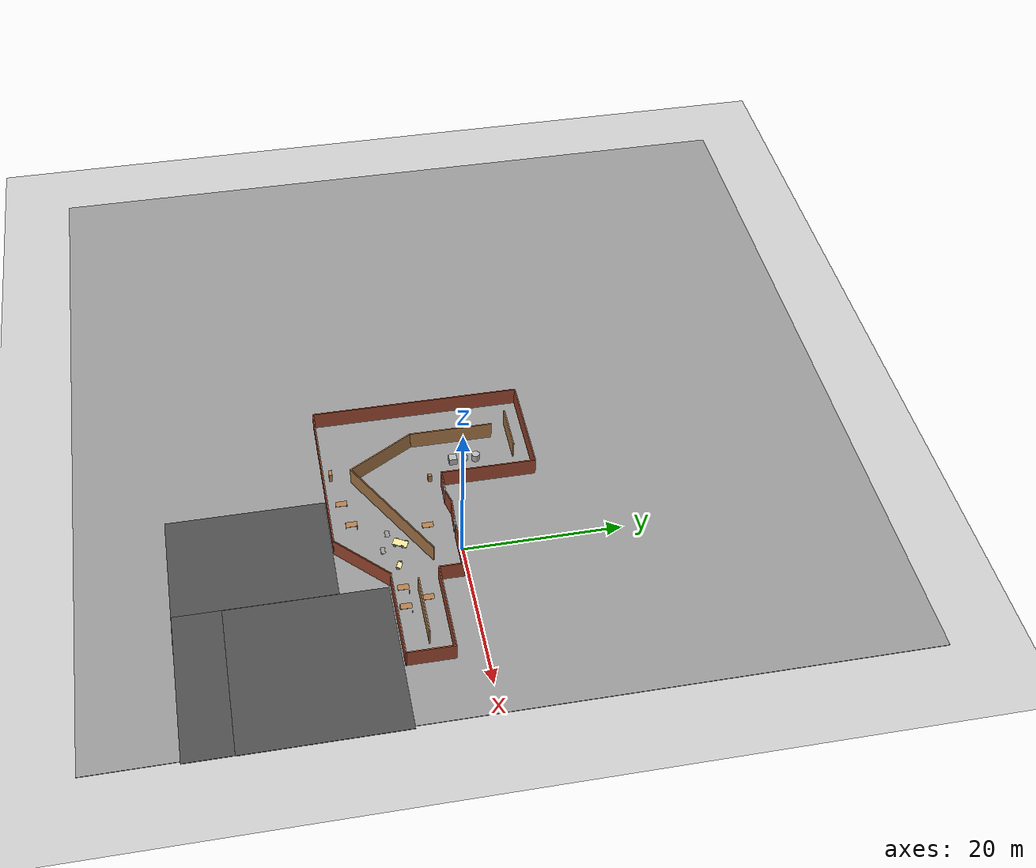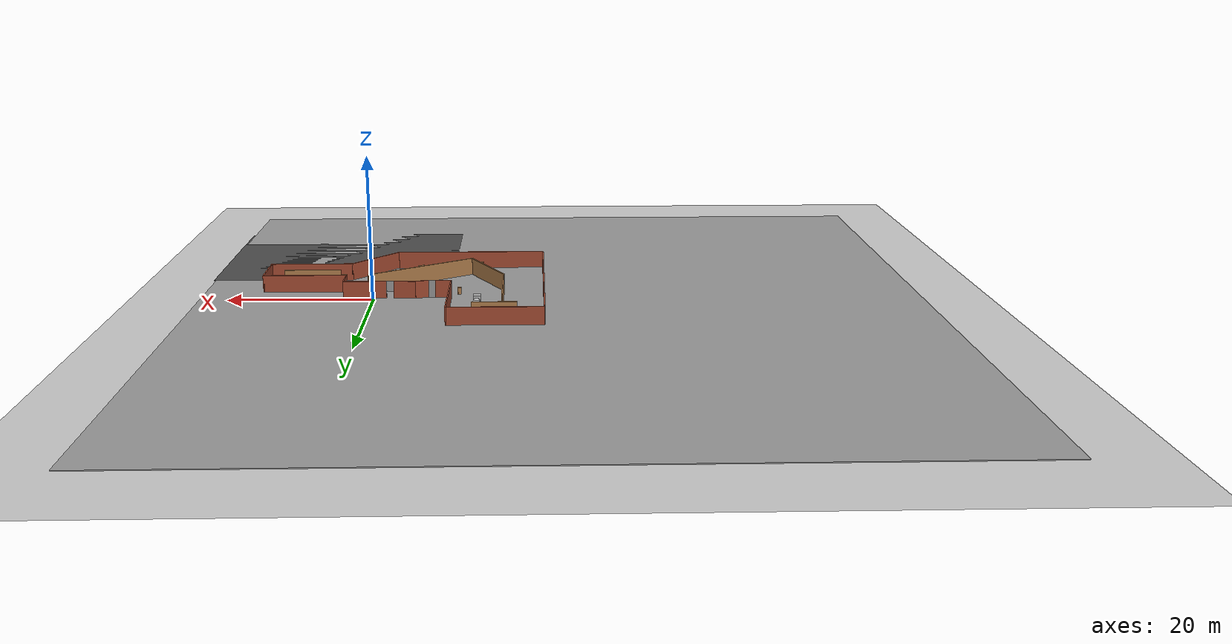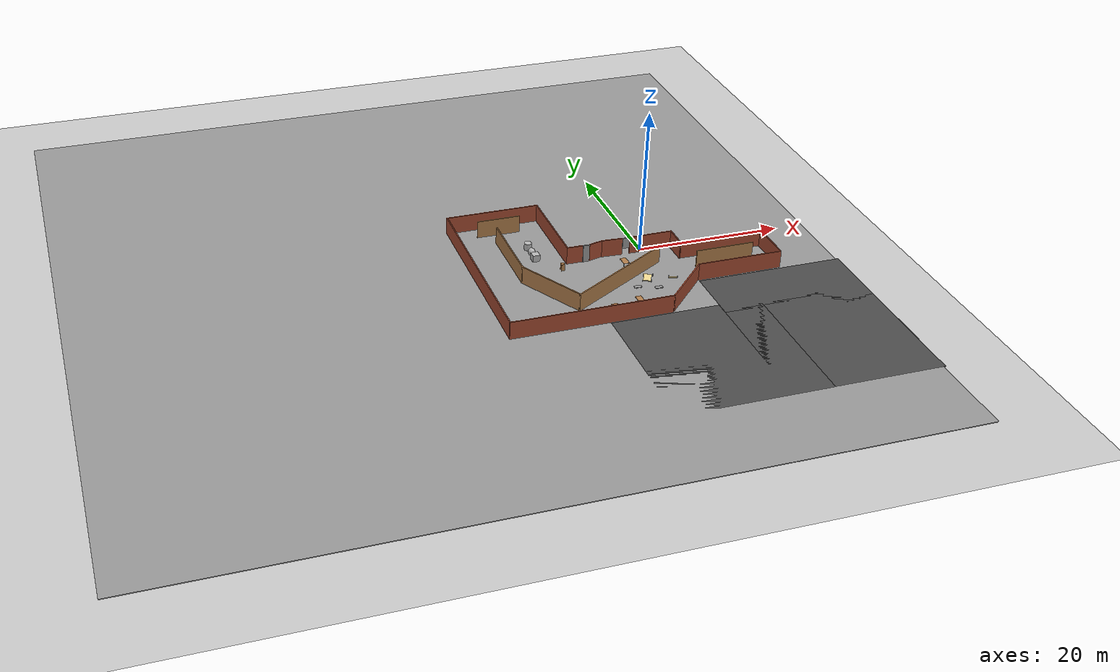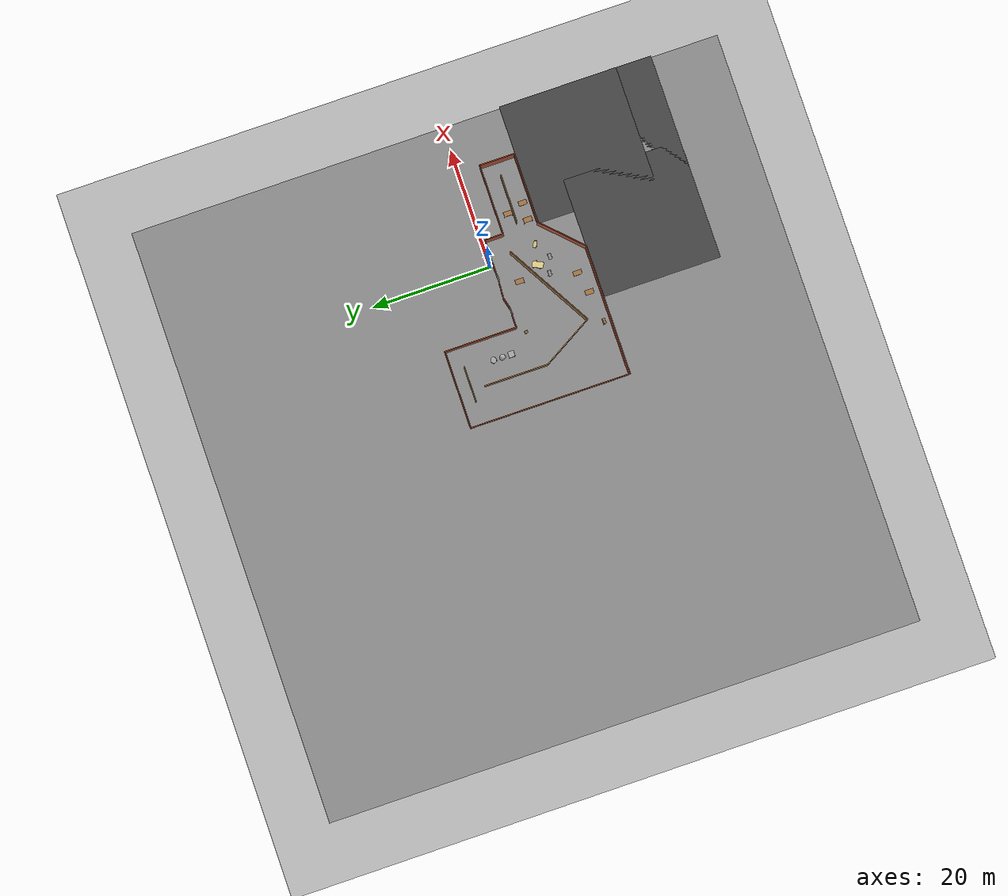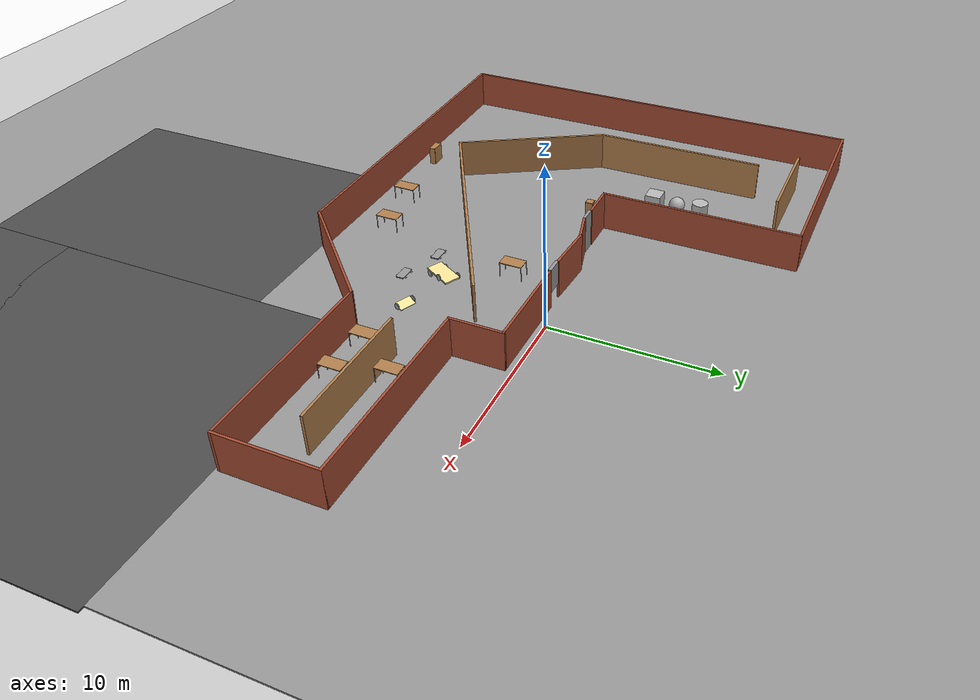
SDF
<sdf version="1.6">
 <world name="default">
  <plugin name="hello" filename="libhello.so"/>
  <model name="ground_plane">
   <static>1</static>
   <link name="link">
    <collision name="collision">
     <geometry><plane><normal>0 0 1</normal><size>100 100</size></plane></geometry>
     <surface><friction><ode><mu>100</mu><mu2>50</mu2></ode></friction></surface>
    </collision>
    <visual name="visual">
     <cast_shadows>0</cast_shadows>
     <geometry><plane><normal>0 0 1</normal><size>100 100</size></plane></geometry>
     <material>
      <script><uri>file://media/materials/scripts/gazebo.material</uri><name>Gazebo/Grey</name></script>
     </material>
    </visual>
   </link>
  </model>
  <gravity>0 0 -9.8</gravity>
  <magnetic_field>6e-06 2.3e-05 -4.2e-05</magnetic_field>
  <atmosphere type="adiabatic"/>
  <physics name="default_physics" default="0" type="ode">
   <max_step_size>0.001</max_step_size>
   <real_time_factor>1</real_time_factor>
   <real_time_update_rate>1000</real_time_update_rate>
  </physics>
  <scene><ambient>0.4 0.4 0.4 1</ambient><background>0.7 0.7 0.7 1</background><shadows>1</shadows></scene>
  <spherical_coordinates>
   <surface_model>EARTH_WGS84</surface_model>
   <latitude_deg>0</latitude_deg>
   <longitude_deg>0</longitude_deg>
   <elevation>0</elevation>
   <heading_deg>0</heading_deg>
  </spherical_coordinates>
  <model name="table_0">
   <static>0</static>
   <link name="link">
    <collision name="surface">
     <pose>0 0 1 0 -0 0</pose>
     <geometry><box><size>1.5 0.8 0.03</size></box></geometry>
     <surface><friction><ode><mu>0.6</mu><mu2>0.6</mu2></ode></friction></surface>
    </collision>
    <visual name="visual1">
     <pose>0 0 1 0 -0 0</pose>
     <geometry><box><size>1.4 0.8 0.04</size></box></geometry>
     <material>
      <script><uri>file://media/materials/scripts/gazebo.material</uri><name>Gazebo/Wood</name></script>
     </material>
    </visual>
    <collision name="front_left_leg">
     <pose>0.68 0.38 0.5 0 -0 0</pose>
     <geometry><cylinder><radius>0.02</radius><length>1</length></cylinder></geometry>
    </collision>
    <visual name="front_left_leg">
     <pose>0.68 0.38 0.5 0 -0 0</pose>
     <geometry><cylinder><radius>0.02</radius><length>1</length></cylinder></geometry>
     <material>
      <script><uri>file://media/materials/scripts/gazebo.material</uri><name>Gazebo/Grey</name></script>
     </material>
    </visual>
    <collision name="front_right_leg">
     <pose>0.68 -0.38 0.5 0 -0 0</pose>
     <geometry><cylinder><radius>0.02</radius><length>1</length></cylinder></geometry>
    </collision>
    <visual name="front_right_leg">
     <pose>0.68 -0.38 0.5 0 -0 0</pose>
     <geometry><cylinder><radius>0.02</radius><length>1</length></cylinder></geometry>
     <material>
      <script><uri>file://media/materials/scripts/gazebo.material</uri><name>Gazebo/Grey</name></script>
     </material>
    </visual>
    <collision name="back_right_leg">
     <pose>-0.68 -0.38 0.5 0 -0 0</pose>
     <geometry><cylinder><radius>0.02</radius><length>1</length></cylinder></geometry>
    </collision>
    <visual name="back_right_leg">
     <pose>-0.68 -0.38 0.5 0 -0 0</pose>
     <geometry><cylinder><radius>0.02</radius><length>1</length></cylinder></geometry>
     <material>
      <script><uri>file://media/materials/scripts/gazebo.material</uri><name>Gazebo/Grey</name></script>
     </material>
    </visual>
    <collision name="back_left_leg">
     <pose>-0.68 0.38 0.5 0 -0 0</pose>
     <geometry><cylinder><radius>0.02</radius><length>1</length></cylinder></geometry>
    </collision>
    <visual name="back_left_leg">
     <pose>-0.68 0.38 0.5 0 -0 0</pose>
     <geometry><cylinder><radius>0.02</radius><length>1</length></cylinder></geometry>
     <material>
      <script><uri>file://media/materials/scripts/gazebo.material</uri><name>Gazebo/Grey</name></script>
     </material>
    </visual>
    <inertial>
     <inertia><ixx>1</ixx><ixy>0</ixy><ixz>0</ixz><iyy>1</iyy><iyz>0</iyz><izz>1</izz></inertia>
     <mass>1</mass>
    </inertial>
   </link>
   <pose>-5.39517 -12.9319 0 0 -0 1.57079</pose>
  </model>
  <model name="table_0_clone">
   <static>0</static>
   <link name="link">
    <collision name="surface">
     <pose>0 0 1 0 -0 0</pose>
     <geometry><box><size>1.5 0.8 0.03</size></box></geometry>
     <surface><friction><ode><mu>0.6</mu><mu2>0.6</mu2></ode></friction></surface>
    </collision>
    <visual name="visual1">
     <pose>0 0 1 0 -0 0</pose>
     <geometry><box><size>1.4 0.8 0.04</size></box></geometry>
     <material>
      <script><uri>file://media/materials/scripts/gazebo.material</uri><name>Gazebo/Wood</name></script>
     </material>
    </visual>
    <collision name="front_left_leg">
     <pose>0.68 0.38 0.5 0 -0 0</pose>
     <geometry><cylinder><radius>0.02</radius><length>1</length></cylinder></geometry>
    </collision>
    <visual name="front_left_leg">
     <pose>0.68 0.38 0.5 0 -0 0</pose>
     <geometry><cylinder><radius>0.02</radius><length>1</length></cylinder></geometry>
     <material>
      <script><uri>file://media/materials/scripts/gazebo.material</uri><name>Gazebo/Grey</name></script>
     </material>
    </visual>
    <collision name="front_right_leg">
     <pose>0.68 -0.38 0.5 0 -0 0</pose>
     <geometry><cylinder><radius>0.02</radius><length>1</length></cylinder></geometry>
    </collision>
    <visual name="front_right_leg">
     <pose>0.68 -0.38 0.5 0 -0 0</pose>
     <geometry><cylinder><radius>0.02</radius><length>1</length></cylinder></geometry>
     <material>
      <script><uri>file://media/materials/scripts/gazebo.material</uri><name>Gazebo/Grey</name></script>
     </material>
    </visual>
    <collision name="back_right_leg">
     <pose>-0.68 -0.38 0.5 0 -0 0</pose>
     <geometry><cylinder><radius>0.02</radius><length>1</length></cylinder></geometry>
    </collision>
    <visual name="back_right_leg">
     <pose>-0.68 -0.38 0.5 0 -0 0</pose>
     <geometry><cylinder><radius>0.02</radius><length>1</length></cylinder></geometry>
     <material>
      <script><uri>file://media/materials/scripts/gazebo.material</uri><name>Gazebo/Grey</name></script>
     </material>
    </visual>
    <collision name="back_left_leg">
     <pose>-0.68 0.38 0.5 0 -0 0</pose>
     <geometry><cylinder><radius>0.02</radius><length>1</length></cylinder></geometry>
    </collision>
    <visual name="back_left_leg">
     <pose>-0.68 0.38 0.5 0 -0 0</pose>
     <geometry><cylinder><radius>0.02</radius><length>1</length></cylinder></geometry>
     <material>
      <script><uri>file://media/materials/scripts/gazebo.material</uri><name>Gazebo/Grey</name></script>
     </material>
    </visual>
    <inertial>
     <inertia><ixx>1</ixx><ixy>0</ixy><ixz>0</ixz><iyy>1</iyy><iyz>0</iyz><izz>1</izz></inertia>
     <mass>1</mass>
    </inertial>
   </link>
   <pose>8.1263 -8.22035 0 0 -0 1.57079</pose>
  </model>
  <model name="table_0_clone_0_clone_0">
   <static>0</static>
   <link name="link">
    <collision name="surface">
     <pose>0 0 1 0 -0 0</pose>
     <geometry><box><size>1.5 0.8 0.03</size></box></geometry>
     <surface><friction><ode><mu>0.6</mu><mu2>0.6</mu2></ode></friction></surface>
    </collision>
    <visual name="visual1">
     <pose>0 0 1 0 -0 0</pose>
     <geometry><box><size>1.4 0.8 0.04</size></box></geometry>
     <material>
      <script><uri>file://media/materials/scripts/gazebo.material</uri><name>Gazebo/Wood</name></script>
     </material>
    </visual>
    <collision name="front_left_leg">
     <pose>0.68 0.38 0.5 0 -0 0</pose>
     <geometry><cylinder><radius>0.02</radius><length>1</length></cylinder></geometry>
    </collision>
    <visual name="front_left_leg">
     <pose>0.68 0.38 0.5 0 -0 0</pose>
     <geometry><cylinder><radius>0.02</radius><length>1</length></cylinder></geometry>
     <material>
      <script><uri>file://media/materials/scripts/gazebo.material</uri><name>Gazebo/Grey</name></script>
     </material>
    </visual>
    <collision name="front_right_leg">
     <pose>0.68 -0.38 0.5 0 -0 0</pose>
     <geometry><cylinder><radius>0.02</radius><length>1</length></cylinder></geometry>
    </collision>
    <visual name="front_right_leg">
     <pose>0.68 -0.38 0.5 0 -0 0</pose>
     <geometry><cylinder><radius>0.02</radius><length>1</length></cylinder></geometry>
     <material>
      <script><uri>file://media/materials/scripts/gazebo.material</uri><name>Gazebo/Grey</name></script>
     </material>
    </visual>
    <collision name="back_right_leg">
     <pose>-0.68 -0.38 0.5 0 -0 0</pose>
     <geometry><cylinder><radius>0.02</radius><length>1</length></cylinder></geometry>
    </collision>
    <visual name="back_right_leg">
     <pose>-0.68 -0.38 0.5 0 -0 0</pose>
     <geometry><cylinder><radius>0.02</radius><length>1</length></cylinder></geometry>
     <material>
      <script><uri>file://media/materials/scripts/gazebo.material</uri><name>Gazebo/Grey</name></script>
     </material>
    </visual>
    <collision name="back_left_leg">
     <pose>-0.68 0.38 0.5 0 -0 0</pose>
     <geometry><cylinder><radius>0.02</radius><length>1</length></cylinder></geometry>
    </collision>
    <visual name="back_left_leg">
     <pose>-0.68 0.38 0.5 0 -0 0</pose>
     <geometry><cylinder><radius>0.02</radius><length>1</length></cylinder></geometry>
     <material>
      <script><uri>file://media/materials/scripts/gazebo.material</uri><name>Gazebo/Grey</name></script>
     </material>
    </visual>
    <inertial>
     <inertia><ixx>1</ixx><ixy>0</ixy><ixz>0</ixz><iyy>1</iyy><iyz>0</iyz><izz>1</izz></inertia>
     <mass>1</mass>
    </inertial>
   </link>
   <pose>5.30131 -8.14232 0 0 -0 1.57081</pose>
  </model>
  <model name="table_0_clone_0_clone_0_clone">
   <static>0</static>
   <link name="link">
    <collision name="surface">
     <pose>0 0 1 0 -0 0</pose>
     <geometry><box><size>1.5 0.8 0.03</size></box></geometry>
     <surface><friction><ode><mu>0.6</mu><mu2>0.6</mu2></ode></friction></surface>
    </collision>
    <visual name="visual1">
     <pose>0 0 1 0 -0 0</pose>
     <geometry><box><size>1.4 0.8 0.04</size></box></geometry>
     <material>
      <script><uri>file://media/materials/scripts/gazebo.material</uri><name>Gazebo/Wood</name></script>
     </material>
    </visual>
    <collision name="front_left_leg">
     <pose>0.68 0.38 0.5 0 -0 0</pose>
     <geometry><cylinder><radius>0.02</radius><length>1</length></cylinder></geometry>
    </collision>
    <visual name="front_left_leg">
     <pose>0.68 0.38 0.5 0 -0 0</pose>
     <geometry><cylinder><radius>0.02</radius><length>1</length></cylinder></geometry>
     <material>
      <script><uri>file://media/materials/scripts/gazebo.material</uri><name>Gazebo/Grey</name></script>
     </material>
    </visual>
    <collision name="front_right_leg">
     <pose>0.68 -0.38 0.5 0 -0 0</pose>
     <geometry><cylinder><radius>0.02</radius><length>1</length></cylinder></geometry>
    </collision>
    <visual name="front_right_leg">
     <pose>0.68 -0.38 0.5 0 -0 0</pose>
     <geometry><cylinder><radius>0.02</radius><length>1</length></cylinder></geometry>
     <material>
      <script><uri>file://media/materials/scripts/gazebo.material</uri><name>Gazebo/Grey</name></script>
     </material>
    </visual>
    <collision name="back_right_leg">
     <pose>-0.68 -0.38 0.5 0 -0 0</pose>
     <geometry><cylinder><radius>0.02</radius><length>1</length></cylinder></geometry>
    </collision>
    <visual name="back_right_leg">
     <pose>-0.68 -0.38 0.5 0 -0 0</pose>
     <geometry><cylinder><radius>0.02</radius><length>1</length></cylinder></geometry>
     <material>
      <script><uri>file://media/materials/scripts/gazebo.material</uri><name>Gazebo/Grey</name></script>
     </material>
    </visual>
    <collision name="back_left_leg">
     <pose>-0.68 0.38 0.5 0 -0 0</pose>
     <geometry><cylinder><radius>0.02</radius><length>1</length></cylinder></geometry>
    </collision>
    <visual name="back_left_leg">
     <pose>-0.68 0.38 0.5 0 -0 0</pose>
     <geometry><cylinder><radius>0.02</radius><length>1</length></cylinder></geometry>
     <material>
      <script><uri>file://media/materials/scripts/gazebo.material</uri><name>Gazebo/Grey</name></script>
     </material>
    </visual>
    <inertial>
     <inertia><ixx>1</ixx><ixy>0</ixy><ixz>0</ixz><iyy>1</iyy><iyz>0</iyz><izz>1</izz></inertia>
     <mass>1</mass>
    </inertial>
   </link>
   <pose>-8.91999 -13.7316 0 0 -0 1.57</pose>
  </model>
  <model name="table_3_clone_clone_clone_0">
   <static>0</static>
   <link name="link">
    <collision name="surface">
     <pose>0 0 1 0 -0 0</pose>
     <geometry><box><size>1.5 0.8 0.03</size></box></geometry>
     <surface><friction><ode><mu>0.6</mu><mu2>0.6</mu2></ode></friction></surface>
    </collision>
    <visual name="visual1">
     <pose>0 0 1 0 -0 0</pose>
     <geometry><box><size>1.4 0.8 0.04</size></box></geometry>
     <material>
      <script><uri>file://media/materials/scripts/gazebo.material</uri><name>Gazebo/Wood</name></script>
     </material>
    </visual>
    <collision name="front_left_leg">
     <pose>0.68 0.38 0.5 0 -0 0</pose>
     <geometry><cylinder><radius>0.02</radius><length>1</length></cylinder></geometry>
    </collision>
    <visual name="front_left_leg">
     <pose>0.68 0.38 0.5 0 -0 0</pose>
     <geometry><cylinder><radius>0.02</radius><length>1</length></cylinder></geometry>
     <material>
      <script><uri>file://media/materials/scripts/gazebo.material</uri><name>Gazebo/Grey</name></script>
     </material>
    </visual>
    <collision name="front_right_leg">
     <pose>0.68 -0.38 0.5 0 -0 0</pose>
     <geometry><cylinder><radius>0.02</radius><length>1</length></cylinder></geometry>
    </collision>
    <visual name="front_right_leg">
     <pose>0.68 -0.38 0.5 0 -0 0</pose>
     <geometry><cylinder><radius>0.02</radius><length>1</length></cylinder></geometry>
     <material>
      <script><uri>file://media/materials/scripts/gazebo.material</uri><name>Gazebo/Grey</name></script>
     </material>
    </visual>
    <collision name="back_right_leg">
     <pose>-0.68 -0.38 0.5 0 -0 0</pose>
     <geometry><cylinder><radius>0.02</radius><length>1</length></cylinder></geometry>
    </collision>
    <visual name="back_right_leg">
     <pose>-0.68 -0.38 0.5 0 -0 0</pose>
     <geometry><cylinder><radius>0.02</radius><length>1</length></cylinder></geometry>
     <material>
      <script><uri>file://media/materials/scripts/gazebo.material</uri><name>Gazebo/Grey</name></script>
     </material>
    </visual>
    <collision name="back_left_leg">
     <pose>-0.68 0.38 0.5 0 -0 0</pose>
     <geometry><cylinder><radius>0.02</radius><length>1</length></cylinder></geometry>
    </collision>
    <visual name="back_left_leg">
     <pose>-0.68 0.38 0.5 0 -0 0</pose>
     <geometry><cylinder><radius>0.02</radius><length>1</length></cylinder></geometry>
     <material>
      <script><uri>file://media/materials/scripts/gazebo.material</uri><name>Gazebo/Grey</name></script>
     </material>
    </visual>
    <inertial>
     <inertia><ixx>1</ixx><ixy>0</ixy><ixz>0</ixz><iyy>1</iyy><iyz>0</iyz><izz>1</izz></inertia>
     <mass>1</mass>
    </inertial>
   </link>
   <pose>-3.69843 -3.68533 0 0 -0 1.57015</pose>
  </model>
  <model name="table_3_clone_clone_clone_0_clone">
   <static>0</static>
   <link name="link">
    <collision name="surface">
     <pose>0 0 1 0 -0 0</pose>
     <geometry><box><size>1.5 0.8 0.03</size></box></geometry>
     <surface><friction><ode><mu>0.6</mu><mu2>0.6</mu2></ode></friction></surface>
    </collision>
    <visual name="visual1">
     <pose>0 0 1 0 -0 0</pose>
     <geometry><box><size>1.4 0.8 0.04</size></box></geometry>
     <material>
      <script><uri>file://media/materials/scripts/gazebo.material</uri><name>Gazebo/Wood</name></script>
     </material>
    </visual>
    <collision name="front_left_leg">
     <pose>0.68 0.38 0.5 0 -0 0</pose>
     <geometry><cylinder><radius>0.02</radius><length>1</length></cylinder></geometry>
    </collision>
    <visual name="front_left_leg">
     <pose>0.68 0.38 0.5 0 -0 0</pose>
     <geometry><cylinder><radius>0.02</radius><length>1</length></cylinder></geometry>
     <material>
      <script><uri>file://media/materials/scripts/gazebo.material</uri><name>Gazebo/Grey</name></script>
     </material>
    </visual>
    <collision name="front_right_leg">
     <pose>0.68 -0.38 0.5 0 -0 0</pose>
     <geometry><cylinder><radius>0.02</radius><length>1</length></cylinder></geometry>
    </collision>
    <visual name="front_right_leg">
     <pose>0.68 -0.38 0.5 0 -0 0</pose>
     <geometry><cylinder><radius>0.02</radius><length>1</length></cylinder></geometry>
     <material>
      <script><uri>file://media/materials/scripts/gazebo.material</uri><name>Gazebo/Grey</name></script>
     </material>
    </visual>
    <collision name="back_right_leg">
     <pose>-0.68 -0.38 0.5 0 -0 0</pose>
     <geometry><cylinder><radius>0.02</radius><length>1</length></cylinder></geometry>
    </collision>
    <visual name="back_right_leg">
     <pose>-0.68 -0.38 0.5 0 -0 0</pose>
     <geometry><cylinder><radius>0.02</radius><length>1</length></cylinder></geometry>
     <material>
      <script><uri>file://media/materials/scripts/gazebo.material</uri><name>Gazebo/Grey</name></script>
     </material>
    </visual>
    <collision name="back_left_leg">
     <pose>-0.68 0.38 0.5 0 -0 0</pose>
     <geometry><cylinder><radius>0.02</radius><length>1</length></cylinder></geometry>
    </collision>
    <visual name="back_left_leg">
     <pose>-0.68 0.38 0.5 0 -0 0</pose>
     <geometry><cylinder><radius>0.02</radius><length>1</length></cylinder></geometry>
     <material>
      <script><uri>file://media/materials/scripts/gazebo.material</uri><name>Gazebo/Grey</name></script>
     </material>
    </visual>
    <inertial>
     <inertia><ixx>1</ixx><ixy>0</ixy><ixz>0</ixz><iyy>1</iyy><iyz>0</iyz><izz>1</izz></inertia>
     <mass>1</mass>
    </inertial>
   </link>
   <pose>7.24861 -5.42889 -2e-06 0 -0 1.57001</pose>
  </model>
  <model name="bookshelf">
   <static>1</static>
   <link name="link">
    <inertial><mass>1</mass></inertial>
    <collision name="back">
     <pose>0 0.005 0.6 0 -0 0</pose>
     <geometry><box><size>0.9 0.01 1.2</size></box></geometry>
    </collision>
    <visual name="visual1">
     <pose>0 0.005 0.6 0 -0 0</pose>
     <geometry><box><size>0.9 0.01 1.2</size></box></geometry>
     <material>
      <script><uri>file://media/materials/scripts/gazebo.material</uri><name>Gazebo/Wood</name></script>
     </material>
    </visual>
    <collision name="left_side">
     <pose>0.45 -0.195 0.6 0 -0 0</pose>
     <geometry><box><size>0.02 0.4 1.2</size></box></geometry>
    </collision>
    <visual name="visual2">
     <pose>0.45 -0.195 0.6 0 -0 0</pose>
     <geometry><box><size>0.02 0.4 1.2</size></box></geometry>
     <material>
      <script><uri>file://media/materials/scripts/gazebo.material</uri><name>Gazebo/Wood</name></script>
     </material>
    </visual>
    <collision name="right_side">
     <pose>-0.45 -0.195 0.6 0 -0 0</pose>
     <geometry><box><size>0.02 0.4 1.2</size></box></geometry>
    </collision>
    <visual name="visual3">
     <pose>-0.45 -0.195 0.6 0 -0 0</pose>
     <geometry><box><size>0.02 0.4 1.2</size></box></geometry>
     <material>
      <script><uri>file://media/materials/scripts/gazebo.material</uri><name>Gazebo/Wood</name></script>
     </material>
    </visual>
    <collision name="bottom">
     <pose>0 -0.195 0.03 0 -0 0</pose>
     <geometry><box><size>0.88 0.4 0.06</size></box></geometry>
    </collision>
    <visual name="visual4">
     <pose>0 -0.195 0.03 0 -0 0</pose>
     <geometry><box><size>0.88 0.4 0.06</size></box></geometry>
     <material>
      <script><uri>file://media/materials/scripts/gazebo.material</uri><name>Gazebo/Wood</name></script>
     </material>
    </visual>
    <collision name="top">
     <pose>0 -0.195 1.19 0 -0 0</pose>
     <geometry><box><size>0.88 0.4 0.02</size></box></geometry>
    </collision>
    <visual name="visual5">
     <pose>0 -0.195 1.19 0 -0 0</pose>
     <geometry><box><size>0.88 0.4 0.02</size></box></geometry>
     <material>
      <script><uri>file://media/materials/scripts/gazebo.material</uri><name>Gazebo/Wood</name></script>
     </material>
    </visual>
    <collision name="low_shelf">
     <pose>0 -0.195 0.43 0 -0 0</pose>
     <geometry><box><size>0.88 0.4 0.02</size></box></geometry>
    </collision>
    <visual name="visual6">
     <pose>0 -0.195 0.43 0 -0 0</pose>
     <geometry><box><size>0.88 0.4 0.02</size></box></geometry>
     <material>
      <script><uri>file://media/materials/scripts/gazebo.material</uri><name>Gazebo/Wood</name></script>
     </material>
    </visual>
    <collision name="high_shelf">
     <pose>0 -0.195 0.8 0 -0 0</pose>
     <geometry><box><size>0.88 0.4 0.02</size></box></geometry>
    </collision>
    <visual name="visual7">
     <pose>0 -0.195 0.8 0 -0 0</pose>
     <geometry><box><size>0.88 0.4 0.02</size></box></geometry>
     <material>
      <script><uri>file://media/materials/scripts/gazebo.material</uri><name>Gazebo/Wood</name></script>
     </material>
    </visual>
   </link>
   <pose>-14.1448 -14.2813 0 0 -0 0</pose>
  </model>
  <model name="cabinet">
   <static>1</static>
   <link name="cabinet_bottom_plate">
    <inertial>
     <pose>0 0 -1 0 -0 0</pose>
     <inertia><ixx>2.05</ixx><ixy>0</ixy><ixz>0</ixz><iyy>2.05</iyy><iyz>0</iyz><izz>2.05</izz></inertia>
     <mass>25</mass>
    </inertial>
    <collision name="cabinet_bottom_plate_geom">
     <pose>0 0 0.01 0 -0 0</pose>
     <geometry><box><size>0.45 0.45 0.02</size></box></geometry>
    </collision>
    <visual name="cabinet_bottom_plate_geom_visual">
     <pose>0 0 0.01 0 -0 0</pose>
     <geometry><box><size>0.45 0.45 0.02</size></box></geometry>
     <material>
      <script><uri>file://media/materials/scripts/gazebo.material</uri><name>Gazebo/Wood</name></script>
     </material>
    </visual>
    <collision name="cabinet_bottom_plate_geom_cabinet_back_plate">
     <pose>0.235 0 0.51 0 -0 0</pose>
     <geometry><box><size>0.02 0.45 1.02</size></box></geometry>
    </collision>
    <visual name="cabinet_bottom_plate_geom_cabinet_back_plate_visual">
     <pose>0.235 0 0.51 0 -0 0</pose>
     <geometry><box><size>0.02 0.45 1.02</size></box></geometry>
     <material>
      <script><uri>file://media/materials/scripts/gazebo.material</uri><name>Gazebo/Wood</name></script>
     </material>
    </visual>
    <collision name="cabinet_bottom_plate_geom_cabinet_left_plate">
     <pose>0 0.235 0.51 0 -0 0</pose>
     <geometry><box><size>0.45 0.02 1.02</size></box></geometry>
    </collision>
    <visual name="cabinet_bottom_plate_geom_cabinet_left_plate_visual">
     <pose>0 0.235 0.51 0 -0 0</pose>
     <geometry><box><size>0.45 0.02 1.02</size></box></geometry>
     <material>
      <script><uri>file://media/materials/scripts/gazebo.material</uri><name>Gazebo/Wood</name></script>
     </material>
    </visual>
    <collision name="cabinet_bottom_plate_geom_cabinet_middle_plate">
     <pose>0 0 0.51 0 -0 0</pose>
     <geometry><box><size>0.45 0.45 0.02</size></box></geometry>
    </collision>
    <visual name="cabinet_bottom_plate_geom_cabinet_middle_plate_visual">
     <pose>0 0 0.51 0 -0 0</pose>
     <geometry><box><size>0.45 0.45 0.02</size></box></geometry>
     <material>
      <script><uri>file://media/materials/scripts/gazebo.material</uri><name>Gazebo/Wood</name></script>
     </material>
    </visual>
    <collision name="cabinet_bottom_plate_geom_cabinet_right_plate">
     <pose>0 -0.235 0.51 0 -0 0</pose>
     <geometry><box><size>0.45 0.02 1.02</size></box></geometry>
    </collision>
    <visual name="cabinet_bottom_plate_geom_cabinet_right_plate_visual">
     <pose>0 -0.235 0.51 0 -0 0</pose>
     <geometry><box><size>0.45 0.02 1.02</size></box></geometry>
     <material>
      <script><uri>file://media/materials/scripts/gazebo.material</uri><name>Gazebo/Wood</name></script>
     </material>
    </visual>
    <collision name="cabinet_bottom_plate_geom_cabinet_top_plate">
     <pose>0 0 1.01 0 -0 0</pose>
     <geometry><box><size>0.45 0.45 0.02</size></box></geometry>
    </collision>
    <visual name="cabinet_bottom_plate_geom_cabinet_top_plate_visual">
     <pose>0 0 1.01 0 -0 0</pose>
     <geometry><box><size>0.45 0.45 0.02</size></box></geometry>
     <material>
      <script><uri>file://media/materials/scripts/gazebo.material</uri><name>Gazebo/Wood</name></script>
     </material>
    </visual>
   </link>
   <pose>-11.7697 -2.07694 0 0 -0 0</pose>
  </model>
  <model name="robot">
   <link name="link_0">
    <pose>0.038001 -0.005114 -0.035369 0 -0 0</pose>
    <inertial>
     <mass>3.09864</mass>
     <inertia>
      <ixx>0.260802</ixx>
      <ixy>0</ixy>
      <ixz>0</ixz>
      <iyy>0.090417</iyy>
      <iyz>0</iyz>
      <izz>0.346055</izz>
     </inertia>
    </inertial>
    <visual name="visual">
     <geometry><box><size>0.583228 1 0.1</size></box></geometry>
     <material>
      <lighting>1</lighting>
      <script><uri>file://media/materials/scripts/gazebo.material</uri><name>Gazebo/Grey</name></script>
      <ambient>1 0.9 0.6 1</ambient>
      <diffuse>1 0.9 0.6 1</diffuse>
      <specular>0.01 0.01 0.01 1</specular>
      <emissive>0 0 0 1</emissive>
      <shader type="vertex"><normal_map>__default__</normal_map></shader>
     </material>
    </visual>
    <collision name="collision">
     <geometry><box><size>0.583228 1 0.1</size></box></geometry>
     <surface>
      <friction>
       <ode><mu>1</mu><mu2>1</mu2><fdir1>0 0 0</fdir1><slip1>0</slip1><slip2>0</slip2></ode>
       <torsional>
        <coefficient>1</coefficient>
        <patch_radius>0</patch_radius>
        <surface_radius>0</surface_radius>
        <use_patch_radius>1</use_patch_radius>
        <ode><slip>0</slip></ode>
       </torsional>
      </friction>
      <bounce><restitution_coefficient>0</restitution_coefficient><threshold>1e+06</threshold></bounce>
      <contact>
       <collide_without_contact>0</collide_without_contact>
       <collide_without_contact_bitmask>1</collide_without_contact_bitmask>
       <collide_bitmask>1</collide_bitmask>
       <ode>
        <soft_cfm>0</soft_cfm>
        <soft_erp>0.2</soft_erp>
        <kp>1e+13</kp>
        <kd>1</kd>
        <max_vel>0.01</max_vel>
        <min_depth>0</min_depth>
       </ode>
       <bullet>
        <split_impulse>1</split_impulse>
        <split_impulse_penetration_threshold>-0.01</split_impulse_penetration_threshold>
        <soft_cfm>0</soft_cfm>
        <soft_erp>0.2</soft_erp>
        <kp>1e+13</kp>
        <kd>1</kd>
       </bullet>
      </contact>
     </surface>
    </collision>
   </link>
   <link name="link_1">
    <pose>-0 -0.550019 0 1.5707 -0 0</pose>
    <inertial>
     <mass>0.499601</mass>
     <inertia>
      <ixx>0.00509991</ixx>
      <ixy>0</ixy>
      <ixz>0</ixz>
      <iyy>0.00509991</iyy>
      <iyz>0</iyz>
      <izz>0.00999201</izz>
     </inertia>
    </inertial>
    <visual name="visual">
     <geometry><cylinder><radius>0.2</radius><length>0.049957</length></cylinder></geometry>
     <material>
      <lighting>1</lighting>
      <script><uri>file://media/materials/scripts/gazebo.material</uri><name>Gazebo/Grey</name></script>
      <ambient>0.5 0.5 0.5 1</ambient>
      <diffuse>0.5 0.5 0.5 1</diffuse>
      <specular>0.01 0.01 0.01 1</specular>
      <emissive>0 0 0 1</emissive>
      <shader type="vertex"><normal_map>__default__</normal_map></shader>
     </material>
    </visual>
    <collision name="collision">
     <geometry><cylinder><radius>0.2</radius><length>0.049957</length></cylinder></geometry>
     <surface>
      <friction>
       <ode><mu>1</mu><mu2>1</mu2><fdir1>0 0 0</fdir1><slip1>0</slip1><slip2>0</slip2></ode>
       <torsional>
        <coefficient>1</coefficient>
        <patch_radius>0</patch_radius>
        <surface_radius>0</surface_radius>
        <use_patch_radius>1</use_patch_radius>
        <ode><slip>0</slip></ode>
       </torsional>
      </friction>
      <bounce><restitution_coefficient>0</restitution_coefficient><threshold>1e+06</threshold></bounce>
      <contact>
       <collide_without_contact>0</collide_without_contact>
       <collide_without_contact_bitmask>1</collide_without_contact_bitmask>
       <collide_bitmask>1</collide_bitmask>
       <ode>
        <soft_cfm>0</soft_cfm>
        <soft_erp>0.2</soft_erp>
        <kp>1e+13</kp>
        <kd>1</kd>
        <max_vel>0.01</max_vel>
        <min_depth>0</min_depth>
       </ode>
       <bullet>
        <split_impulse>1</split_impulse>
        <split_impulse_penetration_threshold>-0.01</split_impulse_penetration_threshold>
        <soft_cfm>0</soft_cfm>
        <soft_erp>0.2</soft_erp>
        <kp>1e+13</kp>
        <kd>1</kd>
       </bullet>
      </contact>
     </surface>
    </collision>
   </link>
   <link name="link_1_clone">
    <pose>0 0.550019 -0 1.5707 -0 0</pose>
    <inertial>
     <mass>0.43298</mass>
     <inertia>
      <ixx>0.00439744</ixx>
      <ixy>0</ixy>
      <ixz>0</ixz>
      <iyy>0.00439744</iyy>
      <iyz>0</iyz>
      <izz>0.00865959</izz>
     </inertia>
    </inertial>
    <visual name="visual">
     <geometry><cylinder><radius>0.2</radius><length>0.0432982</length></cylinder></geometry>
     <material>
      <lighting>1</lighting>
      <script><uri>file://media/materials/scripts/gazebo.material</uri><name>Gazebo/Grey</name></script>
      <ambient>0.5 0.5 0.5 1</ambient>
      <diffuse>0.5 0.5 0.5 1</diffuse>
      <specular>0.01 0.01 0.01 1</specular>
      <emissive>0 0 0 1</emissive>
      <shader type="vertex"><normal_map>__default__</normal_map></shader>
     </material>
    </visual>
    <collision name="collision">
     <geometry><cylinder><radius>0.2</radius><length>0.043298</length></cylinder></geometry>
     <surface>
      <friction>
       <ode><mu>1</mu><mu2>1</mu2><fdir1>0 0 0</fdir1><slip1>0</slip1><slip2>0</slip2></ode>
       <torsional>
        <coefficient>1</coefficient>
        <patch_radius>0</patch_radius>
        <surface_radius>0</surface_radius>
        <use_patch_radius>1</use_patch_radius>
        <ode><slip>0</slip></ode>
       </torsional>
      </friction>
      <bounce><restitution_coefficient>0</restitution_coefficient><threshold>1e+06</threshold></bounce>
      <contact>
       <collide_without_contact>0</collide_without_contact>
       <collide_without_contact_bitmask>1</collide_without_contact_bitmask>
       <collide_bitmask>1</collide_bitmask>
       <ode>
        <soft_cfm>0</soft_cfm>
        <soft_erp>0.2</soft_erp>
        <kp>1e+13</kp>
        <kd>1</kd>
        <max_vel>0.01</max_vel>
        <min_depth>0</min_depth>
       </ode>
       <bullet>
        <split_impulse>1</split_impulse>
        <split_impulse_penetration_threshold>-0.01</split_impulse_penetration_threshold>
        <soft_cfm>0</soft_cfm>
        <soft_erp>0.2</soft_erp>
        <kp>1e+13</kp>
        <kd>1</kd>
       </bullet>
      </contact>
     </surface>
    </collision>
   </link>
   <joint name="link_0_JOINT_0" type="revolute">
    <parent>link_0</parent>
    <child>link_1</child>
    <axis>
     <xyz>0 0 1</xyz>
     <use_parent_model_frame>0</use_parent_model_frame>
     <limit>
      <lower>-1.79769e+308</lower>
      <upper>1.79769e+308</upper>
      <effort>-1</effort>
      <velocity>-1</velocity>
     </limit>
     <dynamics>
      <spring_reference>0</spring_reference>
      <spring_stiffness>0</spring_stiffness>
      <damping>0</damping>
      <friction>0</friction>
     </dynamics>
    </axis>
    <physics>
     <ode><limit><cfm>0</cfm><erp>0.2</erp></limit><suspension><cfm>0</cfm><erp>0.2</erp></suspension></ode>
    </physics>
   </joint>
   <joint name="link_0_JOINT_1" type="revolute">
    <parent>link_0</parent>
    <child>link_1_clone</child>
    <axis>
     <xyz>0 0 1</xyz>
     <use_parent_model_frame>0</use_parent_model_frame>
     <limit>
      <lower>-1.79769e+308</lower>
      <upper>1.79769e+308</upper>
      <effort>-1</effort>
      <velocity>-1</velocity>
     </limit>
     <dynamics>
      <spring_reference>0</spring_reference>
      <spring_stiffness>0</spring_stiffness>
      <damping>0</damping>
      <friction>0</friction>
     </dynamics>
    </axis>
    <physics>
     <ode><limit><cfm>0</cfm><erp>0.2</erp></limit><suspension><cfm>0</cfm><erp>0.2</erp></suspension></ode>
    </physics>
   </joint>
   <static>0</static>
   <pose>1.28995 -8.02668 0.200002 0 0.374406 1.16503</pose>
  </model>
  <model name="wheely">
   <link name="link_0">
    <pose>-0.050655 0.038805 -0.014544 1e-06 0.271798 0.057206</pose>
    <inertial>
     <mass>9.70976</mass>
     <inertia><ixx>0.817238</ixx><ixy>0</ixy><ixz>0</ixz><iyy>2.71066</iyy><iyz>0</iyz><izz>3.51172</izz></inertia>
    </inertial>
    <visual name="visual">
     <geometry><box><size>1.82757 1 0.1</size></box></geometry>
     <material>
      <lighting>1</lighting>
      <script><uri>file://media/materials/scripts/gazebo.material</uri><name>Gazebo/Grey</name></script>
      <ambient>1 0.9 0.6 1</ambient>
      <diffuse>1 0.9 0.6 1</diffuse>
      <specular>0.01 0.01 0.01 1</specular>
      <emissive>0 0 0 1</emissive>
      <shader type="vertex"><normal_map>__default__</normal_map></shader>
     </material>
    </visual>
    <collision name="collision">
     <geometry><box><size>1.82757 1 0.1</size></box></geometry>
     <surface>
      <friction>
       <ode><mu>1</mu><mu2>1</mu2><fdir1>0 0 0</fdir1><slip1>0</slip1><slip2>0</slip2></ode>
       <torsional>
        <coefficient>1</coefficient>
        <patch_radius>0</patch_radius>
        <surface_radius>0</surface_radius>
        <use_patch_radius>1</use_patch_radius>
        <ode><slip>0</slip></ode>
       </torsional>
      </friction>
      <bounce><restitution_coefficient>0</restitution_coefficient><threshold>1e+06</threshold></bounce>
      <contact>
       <collide_without_contact>0</collide_without_contact>
       <collide_without_contact_bitmask>1</collide_without_contact_bitmask>
       <collide_bitmask>1</collide_bitmask>
       <ode>
        <soft_cfm>0</soft_cfm>
        <soft_erp>0.2</soft_erp>
        <kp>1e+13</kp>
        <kd>1</kd>
        <max_vel>0.01</max_vel>
        <min_depth>0</min_depth>
       </ode>
       <bullet>
        <split_impulse>1</split_impulse>
        <split_impulse_penetration_threshold>-0.01</split_impulse_penetration_threshold>
        <soft_cfm>0</soft_cfm>
        <soft_erp>0.2</soft_erp>
        <kp>1e+13</kp>
        <kd>1</kd>
       </bullet>
      </contact>
     </surface>
    </collision>
   </link>
   <link name="link_1">
    <pose>-0.596107 -0.550019 -0 1.5707 -0 0</pose>
    <inertial>
     <mass>0.499601</mass>
     <inertia>
      <ixx>0.00509991</ixx>
      <ixy>0</ixy>
      <ixz>0</ixz>
      <iyy>0.00509991</iyy>
      <iyz>0</iyz>
      <izz>0.00999201</izz>
     </inertia>
    </inertial>
    <visual name="visual">
     <geometry><cylinder><radius>0.2</radius><length>0.049957</length></cylinder></geometry>
     <material>
      <lighting>1</lighting>
      <script><uri>file://media/materials/scripts/gazebo.material</uri><name>Gazebo/Grey</name></script>
      <ambient>0.5 0.5 0.5 1</ambient>
      <diffuse>0.5 0.5 0.5 1</diffuse>
      <specular>0.01 0.01 0.01 1</specular>
      <emissive>0 0 0 1</emissive>
      <shader type="vertex"><normal_map>__default__</normal_map></shader>
     </material>
    </visual>
    <collision name="collision">
     <geometry><cylinder><radius>0.2</radius><length>0.049957</length></cylinder></geometry>
     <surface>
      <friction>
       <ode><mu>1</mu><mu2>1</mu2><fdir1>0 0 0</fdir1><slip1>0</slip1><slip2>0</slip2></ode>
       <torsional>
        <coefficient>1</coefficient>
        <patch_radius>0</patch_radius>
        <surface_radius>0</surface_radius>
        <use_patch_radius>1</use_patch_radius>
        <ode><slip>0</slip></ode>
       </torsional>
      </friction>
      <bounce><restitution_coefficient>0</restitution_coefficient><threshold>1e+06</threshold></bounce>
      <contact>
       <collide_without_contact>0</collide_without_contact>
       <collide_without_contact_bitmask>1</collide_without_contact_bitmask>
       <collide_bitmask>1</collide_bitmask>
       <ode>
        <soft_cfm>0</soft_cfm>
        <soft_erp>0.2</soft_erp>
        <kp>1e+13</kp>
        <kd>1</kd>
        <max_vel>0.01</max_vel>
        <min_depth>0</min_depth>
       </ode>
       <bullet>
        <split_impulse>1</split_impulse>
        <split_impulse_penetration_threshold>-0.01</split_impulse_penetration_threshold>
        <soft_cfm>0</soft_cfm>
        <soft_erp>0.2</soft_erp>
        <kp>1e+13</kp>
        <kd>1</kd>
       </bullet>
      </contact>
     </surface>
    </collision>
   </link>
   <link name="link_1_clone">
    <pose>-0.61948 0.550019 0 1.5707 -0 0</pose>
    <inertial>
     <mass>0.43298</mass>
     <inertia>
      <ixx>0.00439744</ixx>
      <ixy>0</ixy>
      <ixz>0</ixz>
      <iyy>0.00439744</iyy>
      <iyz>0</iyz>
      <izz>0.00865959</izz>
     </inertia>
    </inertial>
    <visual name="visual">
     <geometry><cylinder><radius>0.2</radius><length>0.0432982</length></cylinder></geometry>
     <material>
      <lighting>1</lighting>
      <script><uri>file://media/materials/scripts/gazebo.material</uri><name>Gazebo/Grey</name></script>
      <ambient>0.5 0.5 0.5 1</ambient>
      <diffuse>0.5 0.5 0.5 1</diffuse>
      <specular>0.01 0.01 0.01 1</specular>
      <emissive>0 0 0 1</emissive>
      <shader type="vertex"><normal_map>__default__</normal_map></shader>
     </material>
    </visual>
    <collision name="collision">
     <geometry><cylinder><radius>0.2</radius><length>0.043298</length></cylinder></geometry>
     <surface>
      <friction>
       <ode><mu>1</mu><mu2>1</mu2><fdir1>0 0 0</fdir1><slip1>0</slip1><slip2>0</slip2></ode>
       <torsional>
        <coefficient>1</coefficient>
        <patch_radius>0</patch_radius>
        <surface_radius>0</surface_radius>
        <use_patch_radius>1</use_patch_radius>
        <ode><slip>0</slip></ode>
       </torsional>
      </friction>
      <bounce><restitution_coefficient>0</restitution_coefficient><threshold>1e+06</threshold></bounce>
      <contact>
       <collide_without_contact>0</collide_without_contact>
       <collide_without_contact_bitmask>1</collide_without_contact_bitmask>
       <collide_bitmask>1</collide_bitmask>
       <ode>
        <soft_cfm>0</soft_cfm>
        <soft_erp>0.2</soft_erp>
        <kp>1e+13</kp>
        <kd>1</kd>
        <max_vel>0.01</max_vel>
        <min_depth>0</min_depth>
       </ode>
       <bullet>
        <split_impulse>1</split_impulse>
        <split_impulse_penetration_threshold>-0.01</split_impulse_penetration_threshold>
        <soft_cfm>0</soft_cfm>
        <soft_erp>0.2</soft_erp>
        <kp>1e+13</kp>
        <kd>1</kd>
       </bullet>
      </contact>
     </surface>
    </collision>
   </link>
   <link name="link_1_clone_clone">
    <pose>0.460007 -0.573936 0.098437 1.5 -0 0</pose>
    <inertial>
     <mass>0.43298</mass>
     <inertia>
      <ixx>0.00439744</ixx>
      <ixy>0</ixy>
      <ixz>0</ixz>
      <iyy>0.00439744</iyy>
      <iyz>0</iyz>
      <izz>0.00865959</izz>
     </inertia>
    </inertial>
    <visual name="visual">
     <geometry><cylinder><radius>0.2</radius><length>0.0432982</length></cylinder></geometry>
     <material>
      <lighting>1</lighting>
      <script><uri>file://media/materials/scripts/gazebo.material</uri><name>Gazebo/Grey</name></script>
      <ambient>0.5 0.5 0.5 1</ambient>
      <diffuse>0.5 0.5 0.5 1</diffuse>
      <specular>0.01 0.01 0.01 1</specular>
      <emissive>0 0 0 1</emissive>
      <shader type="vertex"><normal_map>__default__</normal_map></shader>
     </material>
    </visual>
    <collision name="collision">
     <geometry><cylinder><radius>0.2</radius><length>0.043298</length></cylinder></geometry>
     <surface>
      <friction>
       <ode><mu>1</mu><mu2>1</mu2><fdir1>0 0 0</fdir1><slip1>0</slip1><slip2>0</slip2></ode>
       <torsional>
        <coefficient>1</coefficient>
        <patch_radius>0</patch_radius>
        <surface_radius>0</surface_radius>
        <use_patch_radius>1</use_patch_radius>
        <ode><slip>0</slip></ode>
       </torsional>
      </friction>
      <bounce><restitution_coefficient>0</restitution_coefficient><threshold>1e+06</threshold></bounce>
      <contact>
       <collide_without_contact>0</collide_without_contact>
       <collide_without_contact_bitmask>1</collide_without_contact_bitmask>
       <collide_bitmask>1</collide_bitmask>
       <ode>
        <soft_cfm>0</soft_cfm>
        <soft_erp>0.2</soft_erp>
        <kp>1e+13</kp>
        <kd>1</kd>
        <max_vel>0.01</max_vel>
        <min_depth>0</min_depth>
       </ode>
       <bullet>
        <split_impulse>1</split_impulse>
        <split_impulse_penetration_threshold>-0.01</split_impulse_penetration_threshold>
        <soft_cfm>0</soft_cfm>
        <soft_erp>0.2</soft_erp>
        <kp>1e+13</kp>
        <kd>1</kd>
       </bullet>
      </contact>
     </surface>
    </collision>
   </link>
   <link name="link_1_clone_clone_clone_0">
    <pose>0.552681 0.62579 -0.239322 1.5 -0 0</pose>
    <inertial>
     <mass>0.43298</mass>
     <inertia>
      <ixx>0.00439744</ixx>
      <ixy>0</ixy>
      <ixz>0</ixz>
      <iyy>0.00439744</iyy>
      <iyz>0</iyz>
      <izz>0.00865959</izz>
     </inertia>
    </inertial>
    <visual name="visual">
     <geometry><cylinder><radius>0.2</radius><length>0.0432982</length></cylinder></geometry>
     <material>
      <lighting>1</lighting>
      <script><uri>file://media/materials/scripts/gazebo.material</uri><name>Gazebo/Grey</name></script>
      <ambient>0.5 0.5 0.5 1</ambient>
      <diffuse>0.5 0.5 0.5 1</diffuse>
      <specular>0.01 0.01 0.01 1</specular>
      <emissive>0 0 0 1</emissive>
      <shader type="vertex"><normal_map>__default__</normal_map></shader>
     </material>
    </visual>
    <collision name="collision">
     <geometry><cylinder><radius>0.2</radius><length>0.043298</length></cylinder></geometry>
     <surface>
      <friction>
       <ode><mu>1</mu><mu2>1</mu2><fdir1>0 0 0</fdir1><slip1>0</slip1><slip2>0</slip2></ode>
       <torsional>
        <coefficient>1</coefficient>
        <patch_radius>0</patch_radius>
        <surface_radius>0</surface_radius>
        <use_patch_radius>1</use_patch_radius>
        <ode><slip>0</slip></ode>
       </torsional>
      </friction>
      <bounce><restitution_coefficient>0</restitution_coefficient><threshold>1e+06</threshold></bounce>
      <contact>
       <collide_without_contact>0</collide_without_contact>
       <collide_without_contact_bitmask>1</collide_without_contact_bitmask>
       <collide_bitmask>1</collide_bitmask>
       <ode>
        <soft_cfm>0</soft_cfm>
        <soft_erp>0.2</soft_erp>
        <kp>1e+13</kp>
        <kd>1</kd>
        <max_vel>0.01</max_vel>
        <min_depth>0</min_depth>
       </ode>
       <bullet>
        <split_impulse>1</split_impulse>
        <split_impulse_penetration_threshold>-0.01</split_impulse_penetration_threshold>
        <soft_cfm>0</soft_cfm>
        <soft_erp>0.2</soft_erp>
        <kp>1e+13</kp>
        <kd>1</kd>
       </bullet>
      </contact>
     </surface>
    </collision>
   </link>
   <joint name="link_0_JOINT_0_0" type="revolute">
    <parent>link_0</parent>
    <child>link_1_clone_clone_clone_0</child>
    <axis>
     <xyz>1 0 0</xyz>
     <use_parent_model_frame>0</use_parent_model_frame>
     <limit>
      <lower>-1.79769e+308</lower>
      <upper>1.79769e+308</upper>
      <effort>-1</effort>
      <velocity>-1</velocity>
     </limit>
     <dynamics>
      <spring_reference>0</spring_reference>
      <spring_stiffness>0</spring_stiffness>
      <damping>0</damping>
     </dynamics>
    </axis>
    <physics>
     <ode><limit><cfm>0</cfm><erp>0.2</erp></limit><suspension><cfm>0</cfm><erp>0.2</erp></suspension></ode>
    </physics>
   </joint>
   <joint name="link_0_JOINT_0" type="revolute">
    <parent>link_0</parent>
    <child>link_1</child>
    <axis>
     <xyz>0 0 1</xyz>
     <use_parent_model_frame>0</use_parent_model_frame>
     <limit>
      <lower>-1.79769e+308</lower>
      <upper>1.79769e+308</upper>
      <effort>-1</effort>
      <velocity>-1</velocity>
     </limit>
     <dynamics>
      <spring_reference>0</spring_reference>
      <spring_stiffness>0</spring_stiffness>
      <damping>0</damping>
      <friction>0</friction>
     </dynamics>
    </axis>
    <physics>
     <ode><limit><cfm>0</cfm><erp>0.2</erp></limit><suspension><cfm>0</cfm><erp>0.2</erp></suspension></ode>
    </physics>
   </joint>
   <joint name="link_0_JOINT_1_0" type="revolute">
    <parent>link_0</parent>
    <child>link_1_clone_clone</child>
    <axis>
     <xyz>1 0 0</xyz>
     <use_parent_model_frame>0</use_parent_model_frame>
     <limit>
      <lower>-1.79769e+308</lower>
      <upper>1.79769e+308</upper>
      <effort>-1</effort>
      <velocity>-1</velocity>
     </limit>
     <dynamics>
      <spring_reference>0</spring_reference>
      <spring_stiffness>0</spring_stiffness>
      <damping>0</damping>
     </dynamics>
    </axis>
    <physics>
     <ode><limit><cfm>0</cfm><erp>0.2</erp></limit><suspension><cfm>0</cfm><erp>0.2</erp></suspension></ode>
    </physics>
   </joint>
   <joint name="link_0_JOINT_1" type="revolute">
    <parent>link_0</parent>
    <child>link_1_clone</child>
    <axis>
     <xyz>0 0 1</xyz>
     <use_parent_model_frame>0</use_parent_model_frame>
     <limit>
      <lower>-1.79769e+308</lower>
      <upper>1.79769e+308</upper>
      <effort>-1</effort>
      <velocity>-1</velocity>
     </limit>
     <dynamics>
      <spring_reference>0</spring_reference>
      <spring_stiffness>0</spring_stiffness>
      <damping>0</damping>
      <friction>0</friction>
     </dynamics>
    </axis>
    <physics>
     <ode><limit><cfm>0</cfm><erp>0.2</erp></limit><suspension><cfm>0</cfm><erp>0.2</erp></suspension></ode>
    </physics>
   </joint>
   <static>0</static>
   <pose>-1.95016 -7.34255 0.321475 0.00433 -0.201064 1.05743</pose>
  </model>
  <model name="uljansworld">
   <pose>-3.89165 -2.11279 0 0 -0 0</pose>
   <link name="Door_1">
    <collision name="Door_1_Collision">
     <geometry><box><size>0.9 0.17 2.5</size></box></geometry>
     <pose>0 0 1.25 0 -0 0</pose>
    </collision>
    <visual name="Door_1_Visual">
     <pose>0 0 1.25 0 -0 0</pose>
     <geometry><box><size>0.9 0.17 2.5</size></box></geometry>
     <material>
      <script><uri>file://media/materials/scripts/gazebo.material</uri><name>Gazebo/Grey</name></script>
     </material>
    </visual>
    <pose>-4.14572 1.29361 0 0 -0 0</pose>
   </link>
   <link name="Wall_0">
    <collision name="Wall_0_Collision">
     <geometry><box><size>6 0.15 2.5</size></box></geometry>
     <pose>0 0 1.25 0 -0 0</pose>
    </collision>
    <visual name="Wall_0_Visual">
     <pose>0 0 1.25 0 -0 0</pose>
     <geometry><box><size>6 0.15 2.5</size></box></geometry>
     <material>
      <script><uri>file://media/materials/scripts/gazebo.material</uri><name>Gazebo/Bricks</name></script>
      <ambient>1 1 1 1</ambient>
     </material>
     <meta><layer>0</layer></meta>
    </visual>
    <pose>5.11556 1.62165 0 0 -0 0</pose>
   </link>
   <link name="Wall_1">
    <collision name="Wall_1_Collision">
     <geometry><box><size>3.25 0.15 2.5</size></box></geometry>
     <pose>0 0 1.25 0 -0 0</pose>
    </collision>
    <visual name="Wall_1_Visual">
     <pose>0 0 1.25 0 -0 0</pose>
     <geometry><box><size>3.25 0.15 2.5</size></box></geometry>
     <material>
      <script><uri>file://media/materials/scripts/gazebo.material</uri><name>Gazebo/Bricks</name></script>
      <ambient>1 1 1 1</ambient>
     </material>
     <meta><layer>0</layer></meta>
    </visual>
    <pose>8.04056 0.071651 0 0 -0 -1.5708</pose>
   </link>
   <link name="Wall_11">
    <collision name="Wall_11_Collision">
     <geometry><box><size>8 0.15 2.5</size></box></geometry>
     <pose>0 0 1.25 0 -0 0</pose>
    </collision>
    <visual name="Wall_11_Visual">
     <pose>0 0 1.25 0 -0 0</pose>
     <geometry><box><size>8 0.15 2.5</size></box></geometry>
     <material>
      <script><uri>file://media/materials/scripts/gazebo.material</uri><name>Gazebo/Wood</name></script>
      <ambient>1 1 1 1</ambient>
     </material>
     <meta><layer>0</layer></meta>
    </visual>
    <pose>13.195 -4.16753 0 0 -0 0</pose>
   </link>
   <link name="Wall_13">
    <collision name="Wall_13_Collision">
     <geometry><box><size>16.5 0.15 2.5</size></box></geometry>
     <pose>0 0 1.25 0 -0 0</pose>
    </collision>
    <visual name="Wall_13_Visual">
     <pose>0 0 1.25 0 -0 0</pose>
     <geometry><box><size>16.5 0.15 2.5</size></box></geometry>
     <material>
      <script><uri>file://media/materials/scripts/gazebo.material</uri><name>Gazebo/Wood</name></script>
      <ambient>1 1 1 1</ambient>
     </material>
     <meta><layer>0</layer></meta>
    </visual>
    <pose>-2.12241 -5.73254 0 0 -0 -2.61799</pose>
   </link>
   <link name="Wall_14">
    <collision name="Wall_14_Collision">
     <geometry><box><size>9.75 0.15 2.5</size></box></geometry>
     <pose>0 0 1.25 0 -0 0</pose>
    </collision>
    <visual name="Wall_14_Visual">
     <pose>0 0 1.25 0 -0 0</pose>
     <geometry><box><size>9.75 0.15 2.5</size></box></geometry>
     <material>
      <script><uri>file://media/materials/scripts/gazebo.material</uri><name>Gazebo/Wood</name></script>
      <ambient>1 1 1 1</ambient>
     </material>
     <meta><layer>0</layer></meta>
    </visual>
    <pose>-11.6022 -5.66312 0 0 -0 2.0944</pose>
   </link>
   <link name="Wall_15">
    <collision name="Wall_15_Collision">
     <geometry><box><size>10.75 0.15 2.5</size></box></geometry>
     <pose>0 0 1.25 0 -0 0</pose>
    </collision>
    <visual name="Wall_15_Visual">
     <pose>0 0 1.25 0 -0 0</pose>
     <geometry><box><size>10.75 0.15 2.5</size></box></geometry>
     <material>
      <script><uri>file://media/materials/scripts/gazebo.material</uri><name>Gazebo/Wood</name></script>
      <ambient>1 1 1 1</ambient>
     </material>
     <meta><layer>0</layer></meta>
    </visual>
    <pose>-14.0022 3.7938 0 0 -0 1.5708</pose>
   </link>
   <link name="Wall_18">
    <collision name="Wall_18_Collision">
     <geometry><box><size>6 0.15 2.5</size></box></geometry>
     <pose>0 0 1.25 0 -0 0</pose>
    </collision>
    <visual name="Wall_18_Visual">
     <pose>0 0 1.25 0 -0 0</pose>
     <geometry><box><size>6 0.15 2.5</size></box></geometry>
     <material>
      <script><uri>file://media/materials/scripts/gazebo.material</uri><name>Gazebo/Wood</name></script>
      <ambient>1 1 1 1</ambient>
     </material>
     <meta><layer>0</layer></meta>
    </visual>
    <pose>-13.0299 11.2929 0 0 -0 0</pose>
   </link>
   <link name="Wall_2">
    <collision name="Wall_2_Collision">
     <geometry><box><size>11.75 0.15 2.5</size></box></geometry>
     <pose>0 0 1.25 0 -0 0</pose>
    </collision>
    <visual name="Wall_2_Visual">
     <pose>0 0 1.25 0 -0 0</pose>
     <geometry><box><size>11.75 0.15 2.5</size></box></geometry>
     <material>
      <script><uri>file://media/materials/scripts/gazebo.material</uri><name>Gazebo/Bricks</name></script>
      <ambient>1 1 1 1</ambient>
     </material>
     <meta><layer>0</layer></meta>
    </visual>
    <pose>13.8406 -1.47835 0 0 -0 0</pose>
   </link>
   <link name="Wall_20">
    <collision name="Wall_20_Collision">
     <geometry><box><size>3.00454 0.15 2.5</size></box></geometry>
     <pose>0 0 1.25 0 -0 0</pose>
    </collision>
    <visual name="Wall_20_Visual">
     <pose>0 0 1.25 0 -0 0</pose>
     <geometry><box><size>3.00454 0.15 2.5</size></box></geometry>
     <material>
      <script><uri>file://media/materials/scripts/gazebo.material</uri><name>Gazebo/Bricks</name></script>
      <ambient>1 1 1 1</ambient>
     </material>
     <meta><layer>0</layer></meta>
    </visual>
    <pose>-0.404756 1.71841 0 0 -0 3.08519</pose>
   </link>
   <link name="Wall_22">
    <collision name="Wall_22_Collision">
     <geometry><box><size>2.25 0.15 2.5</size></box></geometry>
     <pose>0 0 1.25 0 -0 0</pose>
    </collision>
    <visual name="Wall_22_Visual">
     <pose>0 0 1.25 0 -0 0</pose>
     <geometry><box><size>2.25 0.15 2.5</size></box></geometry>
     <material>
      <script><uri>file://media/materials/scripts/gazebo.material</uri><name>Gazebo/Bricks</name></script>
      <ambient>1 1 1 1</ambient>
     </material>
     <meta><layer>0</layer></meta>
    </visual>
    <pose>-5.74056 1.34053 0 0 -0 0</pose>
   </link>
   <link name="Wall_24">
    <collision name="Wall_24_Collision">
     <geometry><box><size>2 0.15 2.5</size></box></geometry>
     <pose>0 0 1.25 0 -0 0</pose>
    </collision>
    <visual name="Wall_24_Visual">
     <pose>0 0 1.25 0 -0 0</pose>
     <geometry><box><size>2 0.15 2.5</size></box></geometry>
     <material>
      <script><uri>file://media/materials/scripts/gazebo.material</uri><name>Gazebo/Bricks</name></script>
      <ambient>1 1 1 1</ambient>
     </material>
     <meta><layer>0</layer></meta>
    </visual>
    <pose>-2.74335 1.53934 0 0 -0 0.261799</pose>
   </link>
   <link name="Wall_3">
    <collision name="Wall_3_Collision">
     <geometry><box><size>6 0.15 2.5</size></box></geometry>
     <pose>0 0 1.25 0 -0 0</pose>
    </collision>
    <visual name="Wall_3_Visual">
     <pose>0 0 1.25 0 -0 0</pose>
     <geometry><box><size>6 0.15 2.5</size></box></geometry>
     <material>
      <script><uri>file://media/materials/scripts/gazebo.material</uri><name>Gazebo/Bricks</name></script>
      <ambient>1 1 1 1</ambient>
     </material>
     <meta><layer>0</layer></meta>
    </visual>
    <pose>19.6406 -4.40335 0 0 -0 -1.5708</pose>
   </link>
   <link name="Wall_4">
    <collision name="Wall_4_Collision">
     <geometry><box><size>11.75 0.15 2.5</size></box></geometry>
     <pose>0 0 1.25 0 -0 0</pose>
    </collision>
    <visual name="Wall_4_Visual">
     <pose>0 0 1.25 0 -0 0</pose>
     <geometry><box><size>11.75 0.15 2.5</size></box></geometry>
     <material>
      <script><uri>file://media/materials/scripts/gazebo.material</uri><name>Gazebo/Bricks</name></script>
      <ambient>1 1 1 1</ambient>
     </material>
     <meta><layer>0</layer></meta>
    </visual>
    <pose>13.8406 -7.32835 0 0 -0 3.14159</pose>
   </link>
   <link name="Wall_5">
    <collision name="Wall_5_Collision">
     <geometry><box><size>8.75 0.15 2.5</size></box></geometry>
     <pose>0 0 1.25 0 -0 0</pose>
    </collision>
    <visual name="Wall_5_Visual">
     <pose>0 0 1.25 0 -0 0</pose>
     <geometry><box><size>8.75 0.15 2.5</size></box></geometry>
     <material>
      <script><uri>file://media/materials/scripts/gazebo.material</uri><name>Gazebo/Bricks</name></script>
      <ambient>1 1 1 1</ambient>
     </material>
     <meta><layer>0</layer></meta>
    </visual>
    <pose>5 -10.3689 0 0 -0 -2.35619</pose>
   </link>
   <link name="Wall_6">
    <collision name="Wall_6_Collision">
     <geometry><box><size>21.75 0.15 2.5</size></box></geometry>
     <pose>0 0 1.25 0 -0 0</pose>
    </collision>
    <visual name="Wall_6_Visual">
     <pose>0 0 1.25 0 -0 0</pose>
     <geometry><box><size>21.75 0.15 2.5</size></box></geometry>
     <material>
      <script><uri>file://media/materials/scripts/gazebo.material</uri><name>Gazebo/Bricks</name></script>
      <ambient>1 1 1 1</ambient>
     </material>
     <meta><layer>0</layer></meta>
    </visual>
    <pose>-8.84056 -13.4095 0 0 -0 3.14159</pose>
   </link>
   <link name="Wall_7">
    <collision name="Wall_7_Collision">
     <geometry><box><size>27 0.15 2.5</size></box></geometry>
     <pose>0 0 1.25 0 -0 0</pose>
    </collision>
    <visual name="Wall_7_Visual">
     <pose>0 0 1.25 0 -0 0</pose>
     <geometry><box><size>27 0.15 2.5</size></box></geometry>
     <material>
      <script><uri>file://media/materials/scripts/gazebo.material</uri><name>Gazebo/Bricks</name></script>
      <ambient>1 1 1 1</ambient>
     </material>
     <meta><layer>0</layer></meta>
    </visual>
    <pose>-19.6406 0.015532 0 0 -0 1.5708</pose>
   </link>
   <link name="Wall_8">
    <collision name="Wall_8_Collision">
     <geometry><box><size>13 0.15 2.5</size></box></geometry>
     <pose>0 0 1.25 0 -0 0</pose>
    </collision>
    <visual name="Wall_8_Visual">
     <pose>0 0 1.25 0 -0 0</pose>
     <geometry><box><size>13 0.15 2.5</size></box></geometry>
     <material>
      <script><uri>file://media/materials/scripts/gazebo.material</uri><name>Gazebo/Bricks</name></script>
      <ambient>1 1 1 1</ambient>
     </material>
     <meta><layer>0</layer></meta>
    </visual>
    <pose>-13.2156 13.4405 0 0 -0 0</pose>
   </link>
   <link name="Wall_9">
    <collision name="Wall_9_Collision">
     <geometry><box><size>12.25 0.15 2.5</size></box></geometry>
     <pose>0 0 1.25 0 -0 0</pose>
    </collision>
    <visual name="Wall_9_Visual">
     <pose>0 0 1.25 0 -0 0</pose>
     <geometry><box><size>12.25 0.15 2.5</size></box></geometry>
     <material>
      <script><uri>file://media/materials/scripts/gazebo.material</uri><name>Gazebo/Bricks</name></script>
      <ambient>1 1 1 1</ambient>
     </material>
     <meta><layer>0</layer></meta>
    </visual>
    <pose>-6.79056 7.39053 0 0 -0 -1.5708</pose>
   </link>
   <link name="Window_0">
    <collision name="Window_0_Collision">
     <geometry><box><size>1 0.2 1.5</size></box></geometry>
     <pose>0 0 0.75 0 -0 0</pose>
    </collision>
    <visual name="Window_0_Visual">
     <pose>0 0 0.75 0 -0 0</pose>
     <geometry><box><size>1 0.2 1.5</size></box></geometry>
     <material>
      <script><uri>file://media/materials/scripts/gazebo.material</uri><name>Gazebo/Grey</name></script>
     </material>
    </visual>
    <pose>1.5827 1.57844 1 0 -0 0</pose>
   </link>
   <static>1</static>
  </model>
  <model name="asphalt_plane">
   <static>1</static>
   <link name="link">
    <collision name="collision"><geometry><box><size>20 20 0.1</size></box></geometry></collision>
    <visual name="visual">
     <cast_shadows>0</cast_shadows>
     <geometry><box><size>20 20 0.1</size></box></geometry>
     <material>
      <script>
       <uri>model://asphalt_plane/materials/scripts</uri>
       <uri>model://asphalt_plane/materials/textures</uri>
       <name>vrc/asphalt</name>
      </script>
     </material>
    </visual>
   </link>
   <pose>-0.343897 -25.6982 0 0 -0 0</pose>
  </model>
  <model name="asphalt_plane_0">
   <static>1</static>
   <link name="link">
    <collision name="collision"><geometry><box><size>20 20 0.1</size></box></geometry></collision>
    <visual name="visual">
     <cast_shadows>0</cast_shadows>
     <geometry><box><size>20 20 0.1</size></box></geometry>
     <material>
      <script>
       <uri>model://asphalt_plane/materials/scripts</uri>
       <uri>model://asphalt_plane/materials/textures</uri>
       <name>vrc/asphalt</name>
      </script>
     </material>
    </visual>
   </link>
   <pose>14.2845 -19.6978 0 0 -0 0</pose>
  </model>
  <model name="asphalt_plane_1">
   <static>1</static>
   <link name="link">
    <collision name="collision"><geometry><box><size>20 20 0.1</size></box></geometry></collision>
    <visual name="visual">
     <cast_shadows>0</cast_shadows>
     <geometry><box><size>20 20 0.1</size></box></geometry>
     <material>
      <script>
       <uri>model://asphalt_plane/materials/scripts</uri>
       <uri>model://asphalt_plane/materials/textures</uri>
       <name>vrc/asphalt</name>
      </script>
     </material>
    </visual>
   </link>
   <pose>14.2438 -25.6641 0 0 -0 0</pose>
  </model>
  <model name="textured_shapes">
   <pose>-14.3519 2.84821 0.5 0 -0 0</pose>
   <link name="box">
    <pose>0 -1.5 0 0 -0 0</pose>
    <collision name="collision"><geometry><box><size>1 1 1</size></box></geometry></collision>
    <visual name="visual">
     <geometry><box><size>1 1 1</size></box></geometry>
     <material>
      <script>
       <uri>model://textured_shapes/materials/scripts</uri>
       <uri>model://textured_shapes/materials/textures</uri>
       <name>TexturedShape/Squares</name>
      </script>
     </material>
    </visual>
    <inertial>
     <inertia><ixx>1</ixx><ixy>0</ixy><ixz>0</ixz><iyy>1</iyy><iyz>0</iyz><izz>1</izz></inertia>
     <mass>1</mass>
    </inertial>
   </link>
   <link name="sphere">
    <collision name="collision"><geometry><sphere><radius>0.5</radius></sphere></geometry></collision>
    <visual name="visual">
     <geometry><sphere><radius>0.5</radius></sphere></geometry>
     <material>
      <script>
       <uri>model://textured_shapes/materials/scripts</uri>
       <uri>model://textured_shapes/materials/textures</uri>
       <name>TexturedShape/Squares</name>
      </script>
     </material>
    </visual>
    <inertial>
     <inertia><ixx>1</ixx><ixy>0</ixy><ixz>0</ixz><iyy>1</iyy><iyz>0</iyz><izz>1</izz></inertia>
     <mass>1</mass>
    </inertial>
   </link>
   <link name="cylinder">
    <pose>0 1.5 0 0 -0 0</pose>
    <collision name="collision">
     <geometry><cylinder><radius>0.5</radius><length>1</length></cylinder></geometry>
    </collision>
    <visual name="visual">
     <geometry><cylinder><radius>0.5</radius><length>1</length></cylinder></geometry>
     <material>
      <script>
       <uri>model://textured_shapes/materials/scripts</uri>
       <uri>model://textured_shapes/materials/textures</uri>
       <name>TexturedShape/Squares</name>
      </script>
     </material>
    </visual>
    <inertial>
     <inertia><ixx>1</ixx><ixy>0</ixy><ixz>0</ixz><iyy>1</iyy><iyz>0</iyz><izz>1</izz></inertia>
     <mass>1</mass>
    </inertial>
   </link>
  </model>
  <model name="ground_plane_0">
   <static>1</static>
   <link name="link">
    <collision name="collision">
     <geometry><plane><normal>0 0 1</normal><size>100 100</size></plane></geometry>
     <surface>
      <contact><collide_bitmask>65535</collide_bitmask></contact>
      <friction><ode><mu>100</mu><mu2>50</mu2></ode></friction>
     </surface>
    </collision>
    <visual name="visual">
     <cast_shadows>0</cast_shadows>
     <geometry><plane><normal>0 0 1</normal><size>100 100</size></plane></geometry>
     <material>
      <script><uri>file://media/materials/scripts/gazebo.material</uri><name>Gazebo/Grey</name></script>
     </material>
    </visual>
   </link>
   <pose>-26.0345 3.08148 0 0 -0 0</pose>
  </model>
  <model name="Wheely_robot2">
   <link name="link_0">
    <inertial>
     <mass>1</mass>
     <inertia>
      <ixx>0.166667</ixx>
      <ixy>0</ixy>
      <ixz>0</ixz>
      <iyy>0.166667</iyy>
      <iyz>0</iyz>
      <izz>0.166667</izz>
     </inertia>
    </inertial>
    <pose>0 0.001523 -0.04 0 -0 0</pose>
    <visual name="visual">
     <geometry><box><size>1 0.5 0.3</size></box></geometry>
     <material>
      <lighting>1</lighting>
      <script><uri>file://media/materials/scripts/gazebo.material</uri><name>Gazebo/Grey</name></script>
      <shader type="vertex"><normal_map>__default__</normal_map></shader>
      <ambient>0.3 0.3 0.3 1</ambient>
      <diffuse>0.7 0.7 0.7 1</diffuse>
      <specular>0.01 0.01 0.01 1</specular>
      <emissive>0 0 0 1</emissive>
     </material>
    </visual>
    <collision name="collision">
     <geometry><box><size>1 0.5 0.3</size></box></geometry>
     <surface>
      <friction>
       <ode><mu>1</mu><mu2>1</mu2><fdir1>0 0 0</fdir1><slip1>0</slip1><slip2>0</slip2></ode>
       <torsional>
        <coefficient>1</coefficient>
        <patch_radius>0</patch_radius>
        <surface_radius>0</surface_radius>
        <use_patch_radius>1</use_patch_radius>
        <ode><slip>0</slip></ode>
       </torsional>
      </friction>
      <bounce><restitution_coefficient>0</restitution_coefficient><threshold>1e+06</threshold></bounce>
      <contact>
       <collide_without_contact>0</collide_without_contact>
       <collide_without_contact_bitmask>1</collide_without_contact_bitmask>
       <collide_bitmask>1</collide_bitmask>
       <ode>
        <soft_cfm>0</soft_cfm>
        <soft_erp>0.2</soft_erp>
        <kp>1e+13</kp>
        <kd>1</kd>
        <max_vel>0.01</max_vel>
        <min_depth>0</min_depth>
       </ode>
       <bullet>
        <split_impulse>1</split_impulse>
        <split_impulse_penetration_threshold>-0.01</split_impulse_penetration_threshold>
        <soft_cfm>0</soft_cfm>
        <soft_erp>0.2</soft_erp>
        <kp>1e+13</kp>
        <kd>1</kd>
       </bullet>
      </contact>
     </surface>
    </collision>
   </link>
   <link name="link_1_clone_0">
    <inertial>
     <mass>1</mass>
     <inertia><ixx>0.145833</ixx><ixy>0</ixy><ixz>0</ixz><iyy>0.145833</iyy><iyz>0</iyz><izz>0.125</izz></inertia>
    </inertial>
    <pose>0.3 -0.298496 -0.14 1.5707 -0 0</pose>
    <visual name="visual">
     <geometry><cylinder><radius>0.2</radius><length>0.1</length></cylinder></geometry>
     <material>
      <lighting>1</lighting>
      <script><uri>file://media/materials/scripts/gazebo.material</uri><name>Gazebo/Grey</name></script>
      <shader type="vertex"><normal_map>__default__</normal_map></shader>
      <ambient>0.3 0.3 0.3 1</ambient>
      <diffuse>0.7 0.7 0.7 1</diffuse>
      <specular>0.01 0.01 0.01 1</specular>
      <emissive>0 0 0 1</emissive>
     </material>
    </visual>
    <collision name="collision">
     <geometry><cylinder><radius>0.2</radius><length>0.1</length></cylinder></geometry>
     <surface>
      <friction>
       <ode><mu>1</mu><mu2>1</mu2><fdir1>0 0 0</fdir1><slip1>0</slip1><slip2>0</slip2></ode>
       <torsional>
        <coefficient>1</coefficient>
        <patch_radius>0</patch_radius>
        <surface_radius>0</surface_radius>
        <use_patch_radius>1</use_patch_radius>
        <ode><slip>0</slip></ode>
       </torsional>
      </friction>
      <bounce><restitution_coefficient>0</restitution_coefficient><threshold>1e+06</threshold></bounce>
      <contact>
       <collide_without_contact>0</collide_without_contact>
       <collide_without_contact_bitmask>1</collide_without_contact_bitmask>
       <collide_bitmask>1</collide_bitmask>
       <ode>
        <soft_cfm>0</soft_cfm>
        <soft_erp>0.2</soft_erp>
        <kp>1e+13</kp>
        <kd>1</kd>
        <max_vel>0.01</max_vel>
        <min_depth>0</min_depth>
       </ode>
       <bullet>
        <split_impulse>1</split_impulse>
        <split_impulse_penetration_threshold>-0.01</split_impulse_penetration_threshold>
        <soft_cfm>0</soft_cfm>
        <soft_erp>0.2</soft_erp>
        <kp>1e+13</kp>
        <kd>1</kd>
       </bullet>
      </contact>
     </surface>
    </collision>
   </link>
   <link name="link_1_clone_1">
    <inertial>
     <mass>1</mass>
     <inertia><ixx>0.145833</ixx><ixy>0</ixy><ixz>0</ixz><iyy>0.145833</iyy><iyz>0</iyz><izz>0.125</izz></inertia>
    </inertial>
    <pose>-0.3 -0.298496 -0.14 1.5707 -0 0</pose>
    <visual name="visual">
     <geometry><cylinder><radius>0.2</radius><length>0.1</length></cylinder></geometry>
     <material>
      <lighting>1</lighting>
      <script><uri>file://media/materials/scripts/gazebo.material</uri><name>Gazebo/Grey</name></script>
      <shader type="vertex"><normal_map>__default__</normal_map></shader>
      <ambient>0.3 0.3 0.3 1</ambient>
      <diffuse>0.7 0.7 0.7 1</diffuse>
      <specular>0.01 0.01 0.01 1</specular>
      <emissive>0 0 0 1</emissive>
     </material>
    </visual>
    <collision name="collision">
     <geometry><cylinder><radius>0.2</radius><length>0.1</length></cylinder></geometry>
     <surface>
      <friction>
       <ode><mu>1</mu><mu2>1</mu2><fdir1>0 0 0</fdir1><slip1>0</slip1><slip2>0</slip2></ode>
       <torsional>
        <coefficient>1</coefficient>
        <patch_radius>0</patch_radius>
        <surface_radius>0</surface_radius>
        <use_patch_radius>1</use_patch_radius>
        <ode><slip>0</slip></ode>
       </torsional>
      </friction>
      <bounce><restitution_coefficient>0</restitution_coefficient><threshold>1e+06</threshold></bounce>
      <contact>
       <collide_without_contact>0</collide_without_contact>
       <collide_without_contact_bitmask>1</collide_without_contact_bitmask>
       <collide_bitmask>1</collide_bitmask>
       <ode>
        <soft_cfm>0</soft_cfm>
        <soft_erp>0.2</soft_erp>
        <kp>1e+13</kp>
        <kd>1</kd>
        <max_vel>0.01</max_vel>
        <min_depth>0</min_depth>
       </ode>
       <bullet>
        <split_impulse>1</split_impulse>
        <split_impulse_penetration_threshold>-0.01</split_impulse_penetration_threshold>
        <soft_cfm>0</soft_cfm>
        <soft_erp>0.2</soft_erp>
        <kp>1e+13</kp>
        <kd>1</kd>
       </bullet>
      </contact>
     </surface>
    </collision>
   </link>
   <link name="link_1_clone_1_clone">
    <inertial>
     <mass>1</mass>
     <inertia><ixx>0.145833</ixx><ixy>0</ixy><ixz>0</ixz><iyy>0.145833</iyy><iyz>0</iyz><izz>0.125</izz></inertia>
    </inertial>
    <pose>0.3 0.293927 -0.14 1.5707 -0 0</pose>
    <visual name="visual">
     <geometry><cylinder><radius>0.2</radius><length>0.1</length></cylinder></geometry>
     <material>
      <lighting>1</lighting>
      <script><uri>file://media/materials/scripts/gazebo.material</uri><name>Gazebo/Grey</name></script>
      <shader type="vertex"><normal_map>__default__</normal_map></shader>
      <ambient>0.3 0.3 0.3 1</ambient>
      <diffuse>0.7 0.7 0.7 1</diffuse>
      <specular>0.01 0.01 0.01 1</specular>
      <emissive>0 0 0 1</emissive>
     </material>
    </visual>
    <collision name="collision">
     <geometry><cylinder><radius>0.2</radius><length>0.1</length></cylinder></geometry>
     <surface>
      <friction>
       <ode><mu>1</mu><mu2>1</mu2><fdir1>0 0 0</fdir1><slip1>0</slip1><slip2>0</slip2></ode>
       <torsional>
        <coefficient>1</coefficient>
        <patch_radius>0</patch_radius>
        <surface_radius>0</surface_radius>
        <use_patch_radius>1</use_patch_radius>
        <ode><slip>0</slip></ode>
       </torsional>
      </friction>
      <bounce><restitution_coefficient>0</restitution_coefficient><threshold>1e+06</threshold></bounce>
      <contact>
       <collide_without_contact>0</collide_without_contact>
       <collide_without_contact_bitmask>1</collide_without_contact_bitmask>
       <collide_bitmask>1</collide_bitmask>
       <ode>
        <soft_cfm>0</soft_cfm>
        <soft_erp>0.2</soft_erp>
        <kp>1e+13</kp>
        <kd>1</kd>
        <max_vel>0.01</max_vel>
        <min_depth>0</min_depth>
       </ode>
       <bullet>
        <split_impulse>1</split_impulse>
        <split_impulse_penetration_threshold>-0.01</split_impulse_penetration_threshold>
        <soft_cfm>0</soft_cfm>
        <soft_erp>0.2</soft_erp>
        <kp>1e+13</kp>
        <kd>1</kd>
       </bullet>
      </contact>
     </surface>
    </collision>
   </link>
   <link name="link_1_clone_1_clone_0">
    <inertial>
     <mass>1</mass>
     <inertia><ixx>0.145833</ixx><ixy>0</ixy><ixz>0</ixz><iyy>0.145833</iyy><iyz>0</iyz><izz>0.125</izz></inertia>
    </inertial>
    <pose>-0.3 0.301542 -0.14 1.5707 -0 0</pose>
    <visual name="visual">
     <geometry><cylinder><radius>0.2</radius><length>0.1</length></cylinder></geometry>
     <material>
      <lighting>1</lighting>
      <script><uri>file://media/materials/scripts/gazebo.material</uri><name>Gazebo/Grey</name></script>
      <shader type="vertex"><normal_map>__default__</normal_map></shader>
      <ambient>0.3 0.3 0.3 1</ambient>
      <diffuse>0.7 0.7 0.7 1</diffuse>
      <specular>0.01 0.01 0.01 1</specular>
      <emissive>0 0 0 1</emissive>
     </material>
    </visual>
    <collision name="collision">
     <geometry><cylinder><radius>0.2</radius><length>0.1</length></cylinder></geometry>
     <surface>
      <friction>
       <ode><mu>1</mu><mu2>1</mu2><fdir1>0 0 0</fdir1><slip1>0</slip1><slip2>0</slip2></ode>
       <torsional>
        <coefficient>1</coefficient>
        <patch_radius>0</patch_radius>
        <surface_radius>0</surface_radius>
        <use_patch_radius>1</use_patch_radius>
        <ode><slip>0</slip></ode>
       </torsional>
      </friction>
      <bounce><restitution_coefficient>0</restitution_coefficient><threshold>1e+06</threshold></bounce>
      <contact>
       <collide_without_contact>0</collide_without_contact>
       <collide_without_contact_bitmask>1</collide_without_contact_bitmask>
       <collide_bitmask>1</collide_bitmask>
       <ode>
        <soft_cfm>0</soft_cfm>
        <soft_erp>0.2</soft_erp>
        <kp>1e+13</kp>
        <kd>1</kd>
        <max_vel>0.01</max_vel>
        <min_depth>0</min_depth>
       </ode>
       <bullet>
        <split_impulse>1</split_impulse>
        <split_impulse_penetration_threshold>-0.01</split_impulse_penetration_threshold>
        <soft_cfm>0</soft_cfm>
        <soft_erp>0.2</soft_erp>
        <kp>1e+13</kp>
        <kd>1</kd>
       </bullet>
      </contact>
     </surface>
    </collision>
   </link>
   <joint name="link_0_JOINT_1" type="revolute">
    <parent>link_0</parent>
    <child>link_1_clone_0</child>
    <axis>
     <xyz>0 0 1</xyz>
     <use_parent_model_frame>0</use_parent_model_frame>
     <limit>
      <lower>-1.79769e+308</lower>
      <upper>1.79769e+308</upper>
      <effort>-1</effort>
      <velocity>-1</velocity>
     </limit>
     <dynamics>
      <spring_reference>0</spring_reference>
      <spring_stiffness>0</spring_stiffness>
      <damping>0</damping>
      <friction>0</friction>
     </dynamics>
    </axis>
    <physics>
     <ode><limit><cfm>0</cfm><erp>0.2</erp></limit><suspension><cfm>0</cfm><erp>0.2</erp></suspension></ode>
    </physics>
   </joint>
   <joint name="link_0_JOINT_4" type="revolute">
    <parent>link_0</parent>
    <child>link_1_clone_1</child>
    <axis>
     <xyz>0 0 1</xyz>
     <use_parent_model_frame>0</use_parent_model_frame>
     <limit>
      <lower>-1.79769e+308</lower>
      <upper>1.79769e+308</upper>
      <effort>-1</effort>
      <velocity>-1</velocity>
     </limit>
     <dynamics>
      <spring_reference>0</spring_reference>
      <spring_stiffness>0</spring_stiffness>
      <damping>0</damping>
      <friction>0</friction>
     </dynamics>
    </axis>
    <physics>
     <ode><limit><cfm>0</cfm><erp>0.2</erp></limit><suspension><cfm>0</cfm><erp>0.2</erp></suspension></ode>
    </physics>
   </joint>
   <joint name="link_0_JOINT_5" type="revolute">
    <parent>link_0</parent>
    <child>link_1_clone_1_clone</child>
    <axis>
     <xyz>0 0 1</xyz>
     <use_parent_model_frame>0</use_parent_model_frame>
     <limit>
      <lower>-1.79769e+308</lower>
      <upper>1.79769e+308</upper>
      <effort>-1</effort>
      <velocity>-1</velocity>
     </limit>
     <dynamics>
      <spring_reference>0</spring_reference>
      <spring_stiffness>0</spring_stiffness>
      <damping>0</damping>
      <friction>0</friction>
     </dynamics>
    </axis>
    <physics>
     <ode><limit><cfm>0</cfm><erp>0.2</erp></limit><suspension><cfm>0</cfm><erp>0.2</erp></suspension></ode>
    </physics>
   </joint>
   <joint name="link_0_JOINT_6" type="revolute">
    <parent>link_0</parent>
    <child>link_1_clone_1_clone_0</child>
    <axis>
     <xyz>0 0 1</xyz>
     <use_parent_model_frame>0</use_parent_model_frame>
     <limit>
      <lower>-1.79769e+308</lower>
      <upper>1.79769e+308</upper>
      <effort>-1</effort>
      <velocity>-1</velocity>
     </limit>
     <dynamics>
      <spring_reference>0</spring_reference>
      <spring_stiffness>0</spring_stiffness>
      <damping>0</damping>
      <friction>0</friction>
     </dynamics>
    </axis>
    <physics>
     <ode><limit><cfm>0</cfm><erp>0.2</erp></limit><suspension><cfm>0</cfm><erp>0.2</erp></suspension></ode>
    </physics>
   </joint>
   <static>0</static>
   <pose>-3.90157 -8.74744 0 0 -0 0</pose>
  </model>
  <model name="Wheely_3">
   <link name="link_0">
    <inertial>
     <mass>1</mass>
     <inertia>
      <ixx>0.166667</ixx>
      <ixy>0</ixy>
      <ixz>0</ixz>
      <iyy>0.166667</iyy>
      <iyz>0</iyz>
      <izz>0.166667</izz>
     </inertia>
    </inertial>
    <pose>-0 0.001523 -0.04 0 -0 0</pose>
    <visual name="visual">
     <geometry><box><size>1 0.5 0.3</size></box></geometry>
     <material>
      <lighting>1</lighting>
      <script><uri>file://media/materials/scripts/gazebo.material</uri><name>Gazebo/Grey</name></script>
      <shader type="vertex"><normal_map>__default__</normal_map></shader>
      <ambient>0.3 0.3 0.3 1</ambient>
      <diffuse>0.7 0.7 0.7 1</diffuse>
      <specular>0.01 0.01 0.01 1</specular>
      <emissive>0 0 0 1</emissive>
     </material>
    </visual>
    <collision name="collision">
     <geometry><box><size>1 0.5 0.3</size></box></geometry>
     <surface>
      <friction>
       <ode><mu>1</mu><mu2>1</mu2><fdir1>0 0 0</fdir1><slip1>0</slip1><slip2>0</slip2></ode>
       <torsional>
        <coefficient>1</coefficient>
        <patch_radius>0</patch_radius>
        <surface_radius>0</surface_radius>
        <use_patch_radius>1</use_patch_radius>
        <ode><slip>0</slip></ode>
       </torsional>
      </friction>
      <bounce><restitution_coefficient>0</restitution_coefficient><threshold>1e+06</threshold></bounce>
      <contact>
       <collide_without_contact>0</collide_without_contact>
       <collide_without_contact_bitmask>1</collide_without_contact_bitmask>
       <collide_bitmask>1</collide_bitmask>
       <ode>
        <soft_cfm>0</soft_cfm>
        <soft_erp>0.2</soft_erp>
        <kp>1e+13</kp>
        <kd>1</kd>
        <max_vel>0.01</max_vel>
        <min_depth>0</min_depth>
       </ode>
       <bullet>
        <split_impulse>1</split_impulse>
        <split_impulse_penetration_threshold>-0.01</split_impulse_penetration_threshold>
        <soft_cfm>0</soft_cfm>
        <soft_erp>0.2</soft_erp>
        <kp>1e+13</kp>
        <kd>1</kd>
       </bullet>
      </contact>
     </surface>
    </collision>
   </link>
   <link name="link_1_clone_0">
    <inertial>
     <mass>1</mass>
     <inertia><ixx>0.145833</ixx><ixy>0</ixy><ixz>0</ixz><iyy>0.145833</iyy><iyz>0</iyz><izz>0.125</izz></inertia>
    </inertial>
    <pose>0.3 -0.298496 -0.14 1.5707 -0 0</pose>
    <visual name="visual">
     <geometry><cylinder><radius>0.2</radius><length>0.1</length></cylinder></geometry>
     <material>
      <lighting>1</lighting>
      <script><uri>file://media/materials/scripts/gazebo.material</uri><name>Gazebo/Grey</name></script>
      <shader type="vertex"><normal_map>__default__</normal_map></shader>
      <ambient>0.3 0.3 0.3 1</ambient>
      <diffuse>0.7 0.7 0.7 1</diffuse>
      <specular>0.01 0.01 0.01 1</specular>
      <emissive>0 0 0 1</emissive>
     </material>
    </visual>
    <collision name="collision">
     <geometry><cylinder><radius>0.2</radius><length>0.1</length></cylinder></geometry>
     <surface>
      <friction>
       <ode><mu>1</mu><mu2>1</mu2><fdir1>0 0 0</fdir1><slip1>0</slip1><slip2>0</slip2></ode>
       <torsional>
        <coefficient>1</coefficient>
        <patch_radius>0</patch_radius>
        <surface_radius>0</surface_radius>
        <use_patch_radius>1</use_patch_radius>
        <ode><slip>0</slip></ode>
       </torsional>
      </friction>
      <bounce><restitution_coefficient>0</restitution_coefficient><threshold>1e+06</threshold></bounce>
      <contact>
       <collide_without_contact>0</collide_without_contact>
       <collide_without_contact_bitmask>1</collide_without_contact_bitmask>
       <collide_bitmask>1</collide_bitmask>
       <ode>
        <soft_cfm>0</soft_cfm>
        <soft_erp>0.2</soft_erp>
        <kp>1e+13</kp>
        <kd>1</kd>
        <max_vel>0.01</max_vel>
        <min_depth>0</min_depth>
       </ode>
       <bullet>
        <split_impulse>1</split_impulse>
        <split_impulse_penetration_threshold>-0.01</split_impulse_penetration_threshold>
        <soft_cfm>0</soft_cfm>
        <soft_erp>0.2</soft_erp>
        <kp>1e+13</kp>
        <kd>1</kd>
       </bullet>
      </contact>
     </surface>
    </collision>
   </link>
   <link name="link_1_clone_1">
    <inertial>
     <mass>1</mass>
     <inertia><ixx>0.145833</ixx><ixy>0</ixy><ixz>0</ixz><iyy>0.145833</iyy><iyz>0</iyz><izz>0.125</izz></inertia>
    </inertial>
    <pose>-0.3 -0.298496 -0.14 1.5707 -0 0</pose>
    <visual name="visual">
     <geometry><cylinder><radius>0.2</radius><length>0.1</length></cylinder></geometry>
     <material>
      <lighting>1</lighting>
      <script><uri>file://media/materials/scripts/gazebo.material</uri><name>Gazebo/Grey</name></script>
      <shader type="vertex"><normal_map>__default__</normal_map></shader>
      <ambient>0.3 0.3 0.3 1</ambient>
      <diffuse>0.7 0.7 0.7 1</diffuse>
      <specular>0.01 0.01 0.01 1</specular>
      <emissive>0 0 0 1</emissive>
     </material>
    </visual>
    <collision name="collision">
     <geometry><cylinder><radius>0.2</radius><length>0.1</length></cylinder></geometry>
     <surface>
      <friction>
       <ode><mu>1</mu><mu2>1</mu2><fdir1>0 0 0</fdir1><slip1>0</slip1><slip2>0</slip2></ode>
       <torsional>
        <coefficient>1</coefficient>
        <patch_radius>0</patch_radius>
        <surface_radius>0</surface_radius>
        <use_patch_radius>1</use_patch_radius>
        <ode><slip>0</slip></ode>
       </torsional>
      </friction>
      <bounce><restitution_coefficient>0</restitution_coefficient><threshold>1e+06</threshold></bounce>
      <contact>
       <collide_without_contact>0</collide_without_contact>
       <collide_without_contact_bitmask>1</collide_without_contact_bitmask>
       <collide_bitmask>1</collide_bitmask>
       <ode>
        <soft_cfm>0</soft_cfm>
        <soft_erp>0.2</soft_erp>
        <kp>1e+13</kp>
        <kd>1</kd>
        <max_vel>0.01</max_vel>
        <min_depth>0</min_depth>
       </ode>
       <bullet>
        <split_impulse>1</split_impulse>
        <split_impulse_penetration_threshold>-0.01</split_impulse_penetration_threshold>
        <soft_cfm>0</soft_cfm>
        <soft_erp>0.2</soft_erp>
        <kp>1e+13</kp>
        <kd>1</kd>
       </bullet>
      </contact>
     </surface>
    </collision>
   </link>
   <link name="link_1_clone_1_clone">
    <inertial>
     <mass>1</mass>
     <inertia><ixx>0.145833</ixx><ixy>0</ixy><ixz>0</ixz><iyy>0.145833</iyy><iyz>0</iyz><izz>0.125</izz></inertia>
    </inertial>
    <pose>0.3 0.293927 -0.14 1.5707 -0 0</pose>
    <visual name="visual">
     <geometry><cylinder><radius>0.2</radius><length>0.1</length></cylinder></geometry>
     <material>
      <lighting>1</lighting>
      <script><uri>file://media/materials/scripts/gazebo.material</uri><name>Gazebo/Grey</name></script>
      <shader type="vertex"><normal_map>__default__</normal_map></shader>
      <ambient>0.3 0.3 0.3 1</ambient>
      <diffuse>0.7 0.7 0.7 1</diffuse>
      <specular>0.01 0.01 0.01 1</specular>
      <emissive>0 0 0 1</emissive>
     </material>
    </visual>
    <collision name="collision">
     <geometry><cylinder><radius>0.2</radius><length>0.1</length></cylinder></geometry>
     <surface>
      <friction>
       <ode><mu>1</mu><mu2>1</mu2><fdir1>0 0 0</fdir1><slip1>0</slip1><slip2>0</slip2></ode>
       <torsional>
        <coefficient>1</coefficient>
        <patch_radius>0</patch_radius>
        <surface_radius>0</surface_radius>
        <use_patch_radius>1</use_patch_radius>
        <ode><slip>0</slip></ode>
       </torsional>
      </friction>
      <bounce><restitution_coefficient>0</restitution_coefficient><threshold>1e+06</threshold></bounce>
      <contact>
       <collide_without_contact>0</collide_without_contact>
       <collide_without_contact_bitmask>1</collide_without_contact_bitmask>
       <collide_bitmask>1</collide_bitmask>
       <ode>
        <soft_cfm>0</soft_cfm>
        <soft_erp>0.2</soft_erp>
        <kp>1e+13</kp>
        <kd>1</kd>
        <max_vel>0.01</max_vel>
        <min_depth>0</min_depth>
       </ode>
       <bullet>
        <split_impulse>1</split_impulse>
        <split_impulse_penetration_threshold>-0.01</split_impulse_penetration_threshold>
        <soft_cfm>0</soft_cfm>
        <soft_erp>0.2</soft_erp>
        <kp>1e+13</kp>
        <kd>1</kd>
       </bullet>
      </contact>
     </surface>
    </collision>
   </link>
   <link name="link_1_clone_1_clone_0">
    <inertial>
     <mass>1</mass>
     <inertia><ixx>0.145833</ixx><ixy>0</ixy><ixz>0</ixz><iyy>0.145833</iyy><iyz>0</iyz><izz>0.125</izz></inertia>
    </inertial>
    <pose>-0.3 0.301542 -0.14 1.5707 -0 0</pose>
    <visual name="visual">
     <geometry><cylinder><radius>0.2</radius><length>0.1</length></cylinder></geometry>
     <material>
      <lighting>1</lighting>
      <script><uri>file://media/materials/scripts/gazebo.material</uri><name>Gazebo/Grey</name></script>
      <shader type="vertex"><normal_map>__default__</normal_map></shader>
      <ambient>0.3 0.3 0.3 1</ambient>
      <diffuse>0.7 0.7 0.7 1</diffuse>
      <specular>0.01 0.01 0.01 1</specular>
      <emissive>0 0 0 1</emissive>
     </material>
    </visual>
    <collision name="collision">
     <geometry><cylinder><radius>0.2</radius><length>0.1</length></cylinder></geometry>
     <surface>
      <friction>
       <ode><mu>1</mu><mu2>1</mu2><fdir1>0 0 0</fdir1><slip1>0</slip1><slip2>0</slip2></ode>
       <torsional>
        <coefficient>1</coefficient>
        <patch_radius>0</patch_radius>
        <surface_radius>0</surface_radius>
        <use_patch_radius>1</use_patch_radius>
        <ode><slip>0</slip></ode>
       </torsional>
      </friction>
      <bounce><restitution_coefficient>0</restitution_coefficient><threshold>1e+06</threshold></bounce>
      <contact>
       <collide_without_contact>0</collide_without_contact>
       <collide_without_contact_bitmask>1</collide_without_contact_bitmask>
       <collide_bitmask>1</collide_bitmask>
       <ode>
        <soft_cfm>0</soft_cfm>
        <soft_erp>0.2</soft_erp>
        <kp>1e+13</kp>
        <kd>1</kd>
        <max_vel>0.01</max_vel>
        <min_depth>0</min_depth>
       </ode>
       <bullet>
        <split_impulse>1</split_impulse>
        <split_impulse_penetration_threshold>-0.01</split_impulse_penetration_threshold>
        <soft_cfm>0</soft_cfm>
        <soft_erp>0.2</soft_erp>
        <kp>1e+13</kp>
        <kd>1</kd>
       </bullet>
      </contact>
     </surface>
    </collision>
   </link>
   <joint name="link_0_JOINT_1" type="revolute">
    <parent>link_0</parent>
    <child>link_1_clone_0</child>
    <axis>
     <xyz>0 0 1</xyz>
     <use_parent_model_frame>0</use_parent_model_frame>
     <limit>
      <lower>-1.79769e+308</lower>
      <upper>1.79769e+308</upper>
      <effort>-1</effort>
      <velocity>-1</velocity>
     </limit>
     <dynamics>
      <spring_reference>0</spring_reference>
      <spring_stiffness>0</spring_stiffness>
      <damping>0</damping>
      <friction>0</friction>
     </dynamics>
    </axis>
    <physics>
     <ode><limit><cfm>0</cfm><erp>0.2</erp></limit><suspension><cfm>0</cfm><erp>0.2</erp></suspension></ode>
    </physics>
   </joint>
   <joint name="link_0_JOINT_4" type="revolute">
    <parent>link_0</parent>
    <child>link_1_clone_1</child>
    <axis>
     <xyz>0 0 1</xyz>
     <use_parent_model_frame>0</use_parent_model_frame>
     <limit>
      <lower>-1.79769e+308</lower>
      <upper>1.79769e+308</upper>
      <effort>-1</effort>
      <velocity>-1</velocity>
     </limit>
     <dynamics>
      <spring_reference>0</spring_reference>
      <spring_stiffness>0</spring_stiffness>
      <damping>0</damping>
      <friction>0</friction>
     </dynamics>
    </axis>
    <physics>
     <ode><limit><cfm>0</cfm><erp>0.2</erp></limit><suspension><cfm>0</cfm><erp>0.2</erp></suspension></ode>
    </physics>
   </joint>
   <joint name="link_0_JOINT_5" type="revolute">
    <parent>link_0</parent>
    <child>link_1_clone_1_clone</child>
    <axis>
     <xyz>0 0 1</xyz>
     <use_parent_model_frame>0</use_parent_model_frame>
     <limit>
      <lower>-1.79769e+308</lower>
      <upper>1.79769e+308</upper>
      <effort>-1</effort>
      <velocity>-1</velocity>
     </limit>
     <dynamics>
      <spring_reference>0</spring_reference>
      <spring_stiffness>0</spring_stiffness>
      <damping>0</damping>
      <friction>0</friction>
     </dynamics>
    </axis>
    <physics>
     <ode><limit><cfm>0</cfm><erp>0.2</erp></limit><suspension><cfm>0</cfm><erp>0.2</erp></suspension></ode>
    </physics>
   </joint>
   <joint name="link_0_JOINT_6" type="revolute">
    <parent>link_0</parent>
    <child>link_1_clone_1_clone_0</child>
    <axis>
     <xyz>0 0 1</xyz>
     <use_parent_model_frame>0</use_parent_model_frame>
     <limit>
      <lower>-1.79769e+308</lower>
      <upper>1.79769e+308</upper>
      <effort>-1</effort>
      <velocity>-1</velocity>
     </limit>
     <dynamics>
      <spring_reference>0</spring_reference>
      <spring_stiffness>0</spring_stiffness>
      <damping>0</damping>
      <friction>0</friction>
     </dynamics>
    </axis>
    <physics>
     <ode><limit><cfm>0</cfm><erp>0.2</erp></limit><suspension><cfm>0</cfm><erp>0.2</erp></suspension></ode>
    </physics>
   </joint>
   <static>0</static>
   <pose>-1.34306 -9.63715 0 0 -0 0</pose>
  </model>
 </world>
</sdf>
